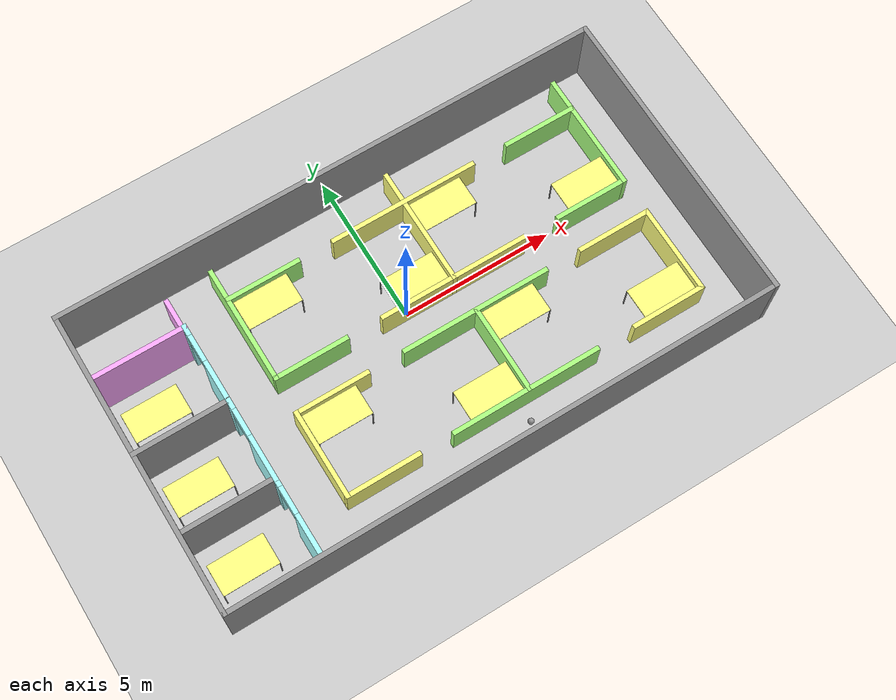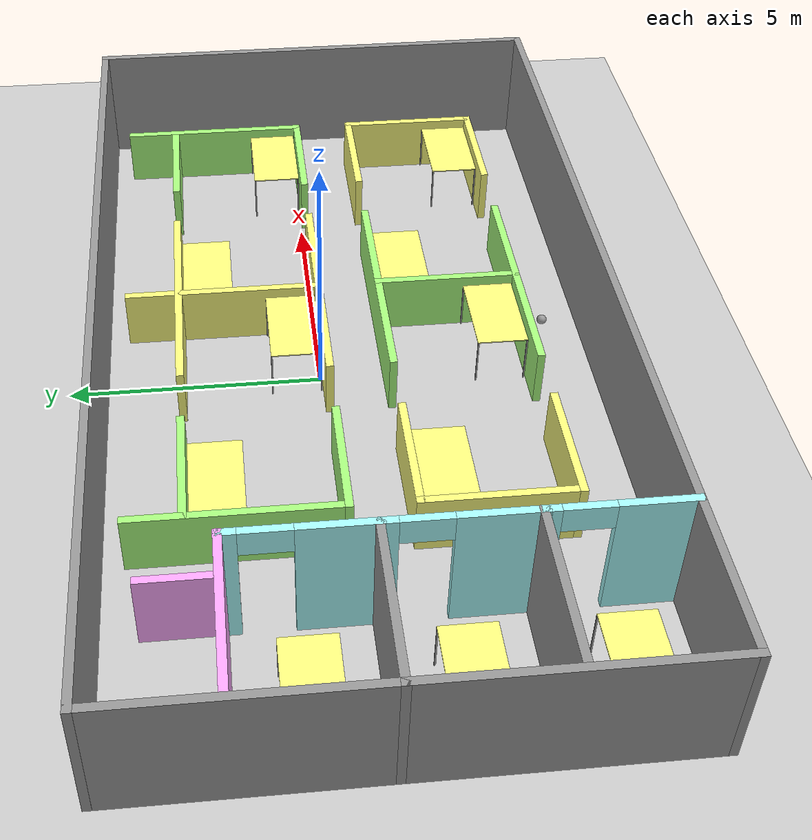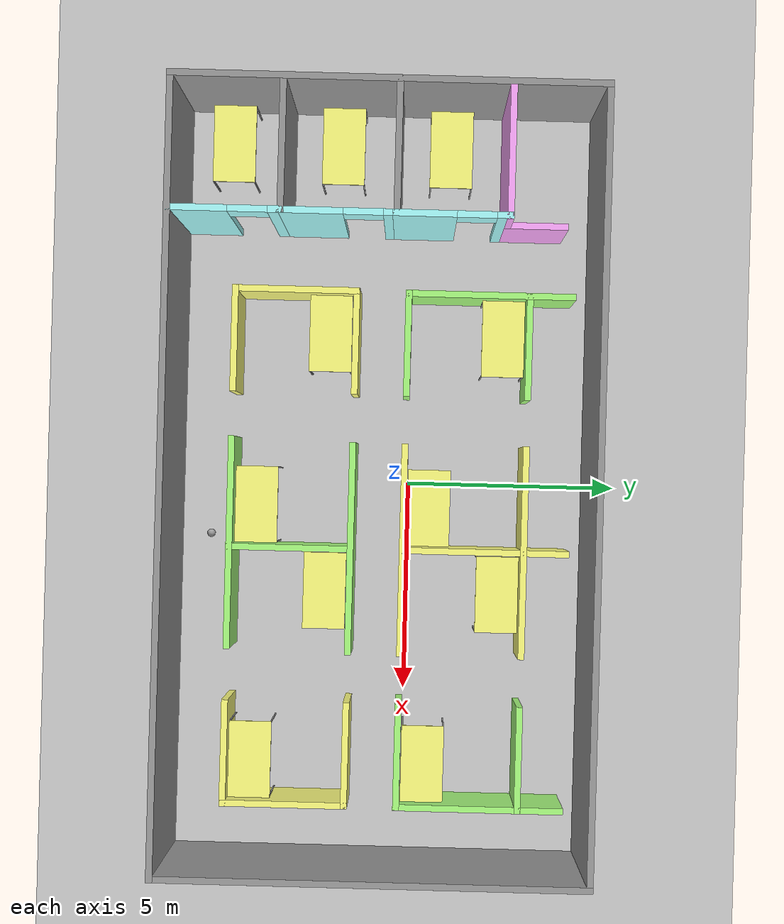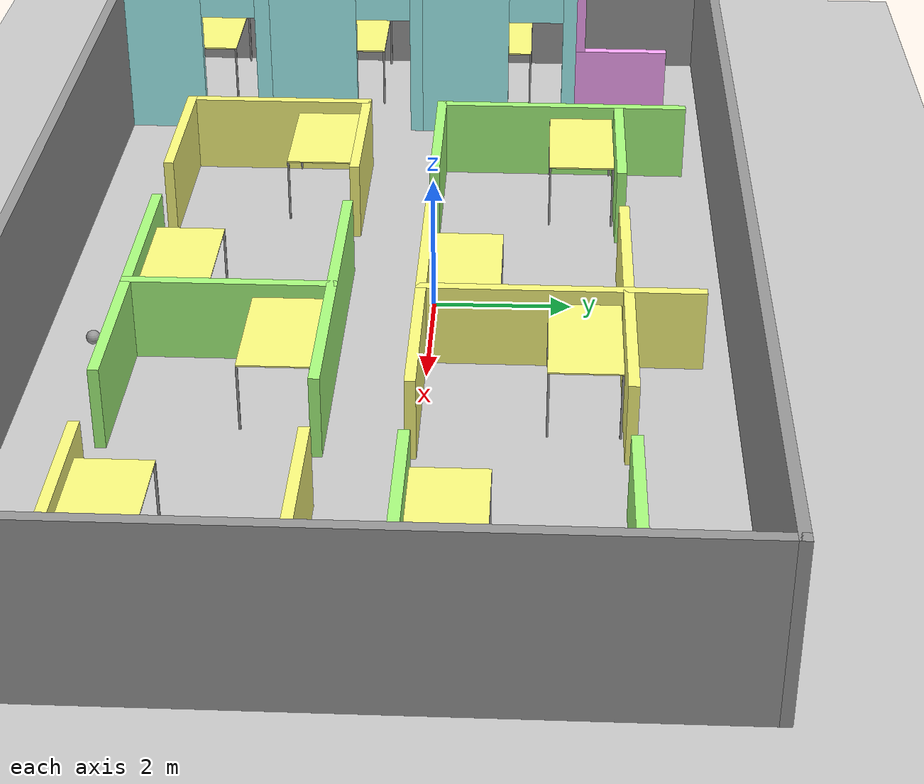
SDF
<sdf version="1.6">
 <world name="default">
  <light name="sun" type="directional">
   <pose>0 0 10 0 -0 0</pose>
   <diffuse>0.8 0.8 0.8 1</diffuse>
   <specular>0.1 0.1 0.1 1</specular>
   <attenuation>
    <range>1000</range>
    <constant>0.9</constant>
    <linear>0.01</linear>
    <quadratic>0.001</quadratic>
   </attenuation>
   <direction>-0.5 0.5 -1</direction>
  </light>
  <model name="ground_plane">
   <static>1</static>
   <link name="link">
    <collision name="collision">
     <geometry><plane><normal>0 0 1</normal><size>100 100</size></plane></geometry>
     <surface><friction><ode><mu>100</mu><mu2>50</mu2></ode></friction></surface>
    </collision>
    <visual name="visual">
     <cast_shadows>0</cast_shadows>
     <geometry><plane><normal>0 0 1</normal><size>100 100</size></plane></geometry>
     <material>
      <script><uri>file://media/materials/scripts/gazebo.material</uri><name>Gazebo/Grey</name></script>
     </material>
    </visual>
   </link>
  </model>
  <gravity>0 0 -9.8</gravity>
  <magnetic_field>6e-06 2.3e-05 -4.2e-05</magnetic_field>
  <atmosphere type="adiabatic"/>
  <physics name="default_physics" default="0" type="ode">
   <max_step_size>0.001</max_step_size>
   <real_time_factor>1</real_time_factor>
   <real_time_update_rate>1000</real_time_update_rate>
  </physics>
  <scene><ambient>0.4 0.4 0.4 1</ambient><background>0.7 0.7 0.7 1</background><shadows>1</shadows></scene>
  <spherical_coordinates>
   <surface_model>EARTH_WGS84</surface_model>
   <latitude_deg>0</latitude_deg>
   <longitude_deg>0</longitude_deg>
   <elevation>0</elevation>
   <heading_deg>0</heading_deg>
  </spherical_coordinates>
  <model name="custom_table">
   <link name="link_0">
    <pose>-1e-06 0 0.4 0 -0 0</pose>
    <inertial>
     <mass>1</mass>
     <inertia>
      <ixx>0.166667</ixx>
      <ixy>0</ixy>
      <ixz>0</ixz>
      <iyy>0.166667</iyy>
      <iyz>0</iyz>
      <izz>0.166667</izz>
     </inertia>
    </inertial>
    <visual name="visual">
     <geometry><box><size>1.8 1 0.02</size></box></geometry>
     <material>
      <lighting>1</lighting>
      <script><uri>file://media/materials/scripts/gazebo.material</uri><name>Gazebo/Grey</name></script>
      <shader type="pixel"><normal_map>__default__</normal_map></shader>
      <ambient>0.4 0.4 0.4 0.5</ambient>
      <diffuse>1 1 0.5 1</diffuse>
      <specular>0.4 0.4 0.4 1</specular>
      <emissive>0 0 0 1</emissive>
     </material>
    </visual>
    <collision name="collision">
     <geometry><box><size>1.8 1 0.02</size></box></geometry>
     <surface>
      <friction>
       <ode><mu>1</mu><mu2>1</mu2><fdir1>0 0 0</fdir1><slip1>0</slip1><slip2>0</slip2></ode>
       <torsional>
        <coefficient>1</coefficient>
        <patch_radius>0</patch_radius>
        <surface_radius>0</surface_radius>
        <use_patch_radius>1</use_patch_radius>
        <ode><slip>0</slip></ode>
       </torsional>
      </friction>
      <bounce><restitution_coefficient>0</restitution_coefficient><threshold>1e+06</threshold></bounce>
      <contact>
       <collide_without_contact>0</collide_without_contact>
       <collide_without_contact_bitmask>1</collide_without_contact_bitmask>
       <collide_bitmask>1</collide_bitmask>
       <ode>
        <soft_cfm>0</soft_cfm>
        <soft_erp>0.2</soft_erp>
        <kp>1e+13</kp>
        <kd>1</kd>
        <max_vel>0.01</max_vel>
        <min_depth>0</min_depth>
       </ode>
       <bullet>
        <split_impulse>1</split_impulse>
        <split_impulse_penetration_threshold>-0.01</split_impulse_penetration_threshold>
        <soft_cfm>0</soft_cfm>
        <soft_erp>0.2</soft_erp>
        <kp>1e+13</kp>
        <kd>1</kd>
       </bullet>
      </contact>
     </surface>
    </collision>
   </link>
   <link name="link_1_clone">
    <pose>0.884999 -0.485 -0.1 0 -0 0</pose>
    <inertial>
     <mass>1</mass>
     <inertia>
      <ixx>0.166667</ixx>
      <ixy>0</ixy>
      <ixz>0</ixz>
      <iyy>0.166667</iyy>
      <iyz>0</iyz>
      <izz>0.166667</izz>
     </inertia>
    </inertial>
    <visual name="visual">
     <geometry><box><size>0.03 0.03 0.98</size></box></geometry>
     <material>
      <lighting>1</lighting>
      <script><uri>file://media/materials/scripts/gazebo.material</uri><name>Gazebo/Grey</name></script>
      <shader type="pixel"><normal_map>__default__</normal_map></shader>
      <ambient>0.3 0.3 0.3 1</ambient>
      <diffuse>0.7 0.7 0.7 1</diffuse>
      <specular>0.01 0.01 0.01 1</specular>
      <emissive>0 0 0 1</emissive>
     </material>
    </visual>
    <collision name="collision">
     <geometry><box><size>0.03 0.03 0.98</size></box></geometry>
     <surface>
      <friction>
       <ode><mu>1</mu><mu2>1</mu2><fdir1>0 0 0</fdir1><slip1>0</slip1><slip2>0</slip2></ode>
       <torsional>
        <coefficient>1</coefficient>
        <patch_radius>0</patch_radius>
        <surface_radius>0</surface_radius>
        <use_patch_radius>1</use_patch_radius>
        <ode><slip>0</slip></ode>
       </torsional>
      </friction>
      <bounce><restitution_coefficient>0</restitution_coefficient><threshold>1e+06</threshold></bounce>
      <contact>
       <collide_without_contact>0</collide_without_contact>
       <collide_without_contact_bitmask>1</collide_without_contact_bitmask>
       <collide_bitmask>1</collide_bitmask>
       <ode>
        <soft_cfm>0</soft_cfm>
        <soft_erp>0.2</soft_erp>
        <kp>1e+13</kp>
        <kd>1</kd>
        <max_vel>0.01</max_vel>
        <min_depth>0</min_depth>
       </ode>
       <bullet>
        <split_impulse>1</split_impulse>
        <split_impulse_penetration_threshold>-0.01</split_impulse_penetration_threshold>
        <soft_cfm>0</soft_cfm>
        <soft_erp>0.2</soft_erp>
        <kp>1e+13</kp>
        <kd>1</kd>
       </bullet>
      </contact>
     </surface>
    </collision>
   </link>
   <link name="link_1_clone_0">
    <pose>-0.885001 0.485 -0.1 0 -0 0</pose>
    <inertial>
     <mass>1</mass>
     <inertia>
      <ixx>0.166667</ixx>
      <ixy>0</ixy>
      <ixz>0</ixz>
      <iyy>0.166667</iyy>
      <iyz>0</iyz>
      <izz>0.166667</izz>
     </inertia>
    </inertial>
    <visual name="visual">
     <geometry><box><size>0.03 0.03 0.98</size></box></geometry>
     <material>
      <lighting>1</lighting>
      <script><uri>file://media/materials/scripts/gazebo.material</uri><name>Gazebo/Grey</name></script>
      <shader type="pixel"><normal_map>__default__</normal_map></shader>
      <ambient>0.3 0.3 0.3 1</ambient>
      <diffuse>0.7 0.7 0.7 1</diffuse>
      <specular>0.01 0.01 0.01 1</specular>
      <emissive>0 0 0 1</emissive>
     </material>
    </visual>
    <collision name="collision">
     <geometry><box><size>0.03 0.03 0.98</size></box></geometry>
     <surface>
      <friction>
       <ode><mu>1</mu><mu2>1</mu2><fdir1>0 0 0</fdir1><slip1>0</slip1><slip2>0</slip2></ode>
       <torsional>
        <coefficient>1</coefficient>
        <patch_radius>0</patch_radius>
        <surface_radius>0</surface_radius>
        <use_patch_radius>1</use_patch_radius>
        <ode><slip>0</slip></ode>
       </torsional>
      </friction>
      <bounce><restitution_coefficient>0</restitution_coefficient><threshold>1e+06</threshold></bounce>
      <contact>
       <collide_without_contact>0</collide_without_contact>
       <collide_without_contact_bitmask>1</collide_without_contact_bitmask>
       <collide_bitmask>1</collide_bitmask>
       <ode>
        <soft_cfm>0</soft_cfm>
        <soft_erp>0.2</soft_erp>
        <kp>1e+13</kp>
        <kd>1</kd>
        <max_vel>0.01</max_vel>
        <min_depth>0</min_depth>
       </ode>
       <bullet>
        <split_impulse>1</split_impulse>
        <split_impulse_penetration_threshold>-0.01</split_impulse_penetration_threshold>
        <soft_cfm>0</soft_cfm>
        <soft_erp>0.2</soft_erp>
        <kp>1e+13</kp>
        <kd>1</kd>
       </bullet>
      </contact>
     </surface>
    </collision>
   </link>
   <link name="link_1_clone_clone">
    <pose>0.884999 0.485 -0.1 0 -0 0</pose>
    <inertial>
     <mass>1</mass>
     <inertia>
      <ixx>0.166667</ixx>
      <ixy>0</ixy>
      <ixz>0</ixz>
      <iyy>0.166667</iyy>
      <iyz>0</iyz>
      <izz>0.166667</izz>
     </inertia>
    </inertial>
    <visual name="visual">
     <geometry><box><size>0.03 0.03 0.98</size></box></geometry>
     <material>
      <lighting>1</lighting>
      <script><uri>file://media/materials/scripts/gazebo.material</uri><name>Gazebo/Grey</name></script>
      <shader type="pixel"><normal_map>__default__</normal_map></shader>
      <ambient>0.3 0.3 0.3 1</ambient>
      <diffuse>0.7 0.7 0.7 1</diffuse>
      <specular>0.01 0.01 0.01 1</specular>
      <emissive>0 0 0 1</emissive>
     </material>
    </visual>
    <collision name="collision">
     <geometry><box><size>0.03 0.03 0.98</size></box></geometry>
     <surface>
      <friction>
       <ode><mu>1</mu><mu2>1</mu2><fdir1>0 0 0</fdir1><slip1>0</slip1><slip2>0</slip2></ode>
       <torsional>
        <coefficient>1</coefficient>
        <patch_radius>0</patch_radius>
        <surface_radius>0</surface_radius>
        <use_patch_radius>1</use_patch_radius>
        <ode><slip>0</slip></ode>
       </torsional>
      </friction>
      <bounce><restitution_coefficient>0</restitution_coefficient><threshold>1e+06</threshold></bounce>
      <contact>
       <collide_without_contact>0</collide_without_contact>
       <collide_without_contact_bitmask>1</collide_without_contact_bitmask>
       <collide_bitmask>1</collide_bitmask>
       <ode>
        <soft_cfm>0</soft_cfm>
        <soft_erp>0.2</soft_erp>
        <kp>1e+13</kp>
        <kd>1</kd>
        <max_vel>0.01</max_vel>
        <min_depth>0</min_depth>
       </ode>
       <bullet>
        <split_impulse>1</split_impulse>
        <split_impulse_penetration_threshold>-0.01</split_impulse_penetration_threshold>
        <soft_cfm>0</soft_cfm>
        <soft_erp>0.2</soft_erp>
        <kp>1e+13</kp>
        <kd>1</kd>
       </bullet>
      </contact>
     </surface>
    </collision>
   </link>
   <link name="link_1_clone_clone_0">
    <pose>-0.885001 -0.485 -0.1 0 -0 0</pose>
    <inertial>
     <mass>1</mass>
     <inertia>
      <ixx>0.166667</ixx>
      <ixy>0</ixy>
      <ixz>0</ixz>
      <iyy>0.166667</iyy>
      <iyz>0</iyz>
      <izz>0.166667</izz>
     </inertia>
    </inertial>
    <visual name="visual">
     <geometry><box><size>0.03 0.03 0.98</size></box></geometry>
     <material>
      <lighting>1</lighting>
      <script><uri>file://media/materials/scripts/gazebo.material</uri><name>Gazebo/Grey</name></script>
      <shader type="pixel"><normal_map>__default__</normal_map></shader>
      <ambient>0.3 0.3 0.3 1</ambient>
      <diffuse>0.7 0.7 0.7 1</diffuse>
      <specular>0.01 0.01 0.01 1</specular>
      <emissive>0 0 0 1</emissive>
     </material>
    </visual>
    <collision name="collision">
     <geometry><box><size>0.03 0.03 0.98</size></box></geometry>
     <surface>
      <friction>
       <ode><mu>1</mu><mu2>1</mu2><fdir1>0 0 0</fdir1><slip1>0</slip1><slip2>0</slip2></ode>
       <torsional>
        <coefficient>1</coefficient>
        <patch_radius>0</patch_radius>
        <surface_radius>0</surface_radius>
        <use_patch_radius>1</use_patch_radius>
        <ode><slip>0</slip></ode>
       </torsional>
      </friction>
      <bounce><restitution_coefficient>0</restitution_coefficient><threshold>1e+06</threshold></bounce>
      <contact>
       <collide_without_contact>0</collide_without_contact>
       <collide_without_contact_bitmask>1</collide_without_contact_bitmask>
       <collide_bitmask>1</collide_bitmask>
       <ode>
        <soft_cfm>0</soft_cfm>
        <soft_erp>0.2</soft_erp>
        <kp>1e+13</kp>
        <kd>1</kd>
        <max_vel>0.01</max_vel>
        <min_depth>0</min_depth>
       </ode>
       <bullet>
        <split_impulse>1</split_impulse>
        <split_impulse_penetration_threshold>-0.01</split_impulse_penetration_threshold>
        <soft_cfm>0</soft_cfm>
        <soft_erp>0.2</soft_erp>
        <kp>1e+13</kp>
        <kd>1</kd>
       </bullet>
      </contact>
     </surface>
    </collision>
   </link>
   <joint name="link_0_JOINT_0" type="fixed">
    <parent>link_0</parent>
    <child>link_1_clone</child>
    <physics>
     <ode><limit><cfm>0</cfm><erp>0.2</erp></limit><suspension><cfm>0</cfm><erp>0.2</erp></suspension></ode>
    </physics>
   </joint>
   <joint name="link_0_JOINT_1" type="fixed">
    <parent>link_0</parent>
    <child>link_1_clone_0</child>
    <physics>
     <ode><limit><cfm>0</cfm><erp>0.2</erp></limit><suspension><cfm>0</cfm><erp>0.2</erp></suspension></ode>
    </physics>
   </joint>
   <joint name="link_0_JOINT_2" type="fixed">
    <parent>link_0</parent>
    <child>link_1_clone_clone</child>
    <physics>
     <ode><limit><cfm>0</cfm><erp>0.2</erp></limit><suspension><cfm>0</cfm><erp>0.2</erp></suspension></ode>
    </physics>
   </joint>
   <joint name="link_0_JOINT_3" type="fixed">
    <parent>link_0</parent>
    <child>link_1_clone_clone_0</child>
    <physics>
     <ode><limit><cfm>0</cfm><erp>0.2</erp></limit><suspension><cfm>0</cfm><erp>0.2</erp></suspension></ode>
    </physics>
   </joint>
   <static>1</static>
   <pose>-7.89321 0.822776 0.6 0 -0 0</pose>
  </model>
  <model name="sr_office">
   <pose>-0.02579 -0.62634 0 0 -0 0</pose>
   <link name="Wall_11">
    <pose>-6.0106 -3.67095 0 0 -0 1.57171</pose>
    <visual name="Wall_11_Visual_0">
     <pose>-0.611587 0 1.25 0 -0 0</pose>
     <geometry><box><size>1.41152 0.15 2.5</size></box></geometry>
     <material>
      <script><uri>file://media/materials/scripts/gazebo.material</uri><name>Gazebo/Grey</name></script>
      <ambient>0.666667 1 1 1</ambient>
     </material>
     <meta><layer>0</layer></meta>
    </visual>
    <collision name="Wall_11_Collision_0">
     <geometry><box><size>1.41152 0.15 2.5</size></box></geometry>
     <pose>-0.611587 0 1.25 0 -0 0</pose>
    </collision>
    <visual name="Wall_11_Visual_1">
     <pose>1.15576 0 1.25 0 -0 0</pose>
     <geometry><box><size>0.323174 0.15 2.5</size></box></geometry>
     <material>
      <script><uri>file://media/materials/scripts/gazebo.material</uri><name>Gazebo/Grey</name></script>
      <ambient>0.666667 1 1 1</ambient>
     </material>
     <meta><layer>0</layer></meta>
    </visual>
    <collision name="Wall_11_Collision_1">
     <geometry><box><size>0.323174 0.15 2.5</size></box></geometry>
     <pose>1.15576 0 1.25 0 -0 0</pose>
    </collision>
    <visual name="Wall_11_Visual_2">
     <pose>0.544173 0 2.25 0 -0 0</pose>
     <geometry><box><size>0.9 0.15 0.5</size></box></geometry>
     <material>
      <script><uri>file://media/materials/scripts/gazebo.material</uri><name>Gazebo/Grey</name></script>
      <ambient>0.666667 1 1 1</ambient>
     </material>
     <meta><layer>0</layer></meta>
    </visual>
    <collision name="Wall_11_Collision_2">
     <geometry><box><size>0.9 0.15 0.5</size></box></geometry>
     <pose>0.544173 0 2.25 0 -0 0</pose>
    </collision>
   </link>
   <link name="Wall_12">
    <collision name="Wall_12_Collision">
     <geometry><box><size>3 0.15 2.5</size></box></geometry>
     <pose>0 0 1.25 0 -0 0</pose>
    </collision>
    <visual name="Wall_12_Visual">
     <pose>0 0 1.25 0 -0 0</pose>
     <geometry><box><size>3 0.15 2.5</size></box></geometry>
     <material>
      <script><uri>file://media/materials/scripts/gazebo.material</uri><name>Gazebo/Grey</name></script>
      <ambient>1 1 1 1</ambient>
     </material>
     <meta><layer>0</layer></meta>
    </visual>
    <pose>-7.43674 -2.38916 0 0 -0 3.14159</pose>
   </link>
   <link name="Wall_19">
    <pose>-6.01174 1.48653 0 0 -0 1.5708</pose>
    <visual name="Wall_19_Visual_0">
     <pose>-0.636752 0 1.25 0 -0 0</pose>
     <geometry><box><size>1.44348 0.15 2.5</size></box></geometry>
     <material>
      <script><uri>file://media/materials/scripts/gazebo.material</uri><name>Gazebo/Grey</name></script>
      <ambient>0.666667 1 1 1</ambient>
     </material>
     <meta><layer>0</layer></meta>
    </visual>
    <collision name="Wall_19_Collision_0">
     <geometry><box><size>1.44348 0.15 2.5</size></box></geometry>
     <pose>-0.636752 0 1.25 0 -0 0</pose>
    </collision>
    <visual name="Wall_19_Visual_1">
     <pose>1.17174 0 1.25 0 -0 0</pose>
     <geometry><box><size>0.373505 0.15 2.5</size></box></geometry>
     <material>
      <script><uri>file://media/materials/scripts/gazebo.material</uri><name>Gazebo/Grey</name></script>
      <ambient>0.666667 1 1 1</ambient>
     </material>
     <meta><layer>0</layer></meta>
    </visual>
    <collision name="Wall_19_Collision_1">
     <geometry><box><size>0.373505 0.15 2.5</size></box></geometry>
     <pose>1.17174 0 1.25 0 -0 0</pose>
    </collision>
    <visual name="Wall_19_Visual_2">
     <pose>0.534986 0 2.25 0 -0 0</pose>
     <geometry><box><size>0.9 0.15 0.5</size></box></geometry>
     <material>
      <script><uri>file://media/materials/scripts/gazebo.material</uri><name>Gazebo/Grey</name></script>
      <ambient>0.666667 1 1 1</ambient>
     </material>
     <meta><layer>0</layer></meta>
    </visual>
    <collision name="Wall_19_Collision_2">
     <geometry><box><size>0.9 0.15 0.5</size></box></geometry>
     <pose>0.534986 0 2.25 0 -0 0</pose>
    </collision>
   </link>
   <link name="Wall_2">
    <collision name="Wall_2_Collision">
     <geometry><box><size>10 0.15 2.5</size></box></geometry>
     <pose>0 0 1.25 0 -0 0</pose>
    </collision>
    <visual name="Wall_2_Visual">
     <pose>0 0 1.25 0 -0 0</pose>
     <geometry><box><size>10 0.15 2.5</size></box></geometry>
     <material>
      <script><uri>file://media/materials/scripts/gazebo.material</uri><name>Gazebo/Grey</name></script>
      <ambient>1 1 1 1</ambient>
     </material>
     <meta><layer>0</layer></meta>
    </visual>
    <pose>-9.01174 2.1e-05 0 0 0 -1.5708</pose>
   </link>
   <link name="Wall_20">
    <collision name="Wall_20_Collision">
     <geometry><box><size>3 0.15 2.5</size></box></geometry>
     <pose>0 0 1.25 0 -0 0</pose>
    </collision>
    <visual name="Wall_20_Visual">
     <pose>0 0 1.25 0 -0 0</pose>
     <geometry><box><size>3 0.15 2.5</size></box></geometry>
     <material>
      <script><uri>file://media/materials/scripts/gazebo.material</uri><name>Gazebo/Grey</name></script>
      <ambient>1 0.666667 1 1</ambient>
     </material>
     <meta><layer>0</layer></meta>
    </visual>
    <pose>-7.43674 2.77002 0 0 -0 3.14159</pose>
   </link>
   <link name="Wall_22">
    <collision name="Wall_22_Collision">
     <geometry><box><size>1.5 0.15 1.5</size></box></geometry>
     <pose>0 0 0.75 0 -0 0</pose>
    </collision>
    <visual name="Wall_22_Visual">
     <pose>0 0 0.75 0 -0 0</pose>
     <geometry><box><size>1.5 0.15 1.5</size></box></geometry>
     <material>
      <script><uri>file://media/materials/scripts/gazebo.material</uri><name>Gazebo/Grey</name></script>
      <ambient>1 0.666667 1 1</ambient>
     </material>
     <meta><layer>0</layer></meta>
    </visual>
    <pose>-6.01174 3.44502 0 0 -0 1.5708</pose>
   </link>
   <link name="Wall_24">
    <collision name="Wall_24_Collision">
     <geometry><box><size>2.5 0.15 1.2</size></box></geometry>
     <pose>0 0 0.6 0 -0 0</pose>
    </collision>
    <visual name="Wall_24_Visual">
     <pose>0 0 0.6 0 -0 0</pose>
     <geometry><box><size>2.5 0.15 1.2</size></box></geometry>
     <material>
      <script><uri>file://media/materials/scripts/gazebo.material</uri><name>Gazebo/Grey</name></script>
      <ambient>1 1 0.498039 1</ambient>
     </material>
     <meta><layer>0</layer></meta>
    </visual>
    <pose>-3.28174 -3.54698 0 0 -0 3.14159</pose>
   </link>
   <link name="Wall_25">
    <collision name="Wall_25_Collision">
     <geometry><box><size>3.0027 0.15 1.2</size></box></geometry>
     <pose>0 0 0.6 0 -0 0</pose>
    </collision>
    <visual name="Wall_25_Visual">
     <pose>0 0 0.6 0 -0 0</pose>
     <geometry><box><size>3.0027 0.15 1.2</size></box></geometry>
     <material>
      <script><uri>file://media/materials/scripts/gazebo.material</uri><name>Gazebo/Grey</name></script>
      <ambient>1 1 0.498039 1</ambient>
     </material>
     <meta><layer>0</layer></meta>
    </visual>
    <pose>-4.45674 -2.12048 0 0 -0 1.5708</pose>
   </link>
   <link name="Wall_26">
    <collision name="Wall_26_Collision">
     <geometry><box><size>2.5 0.15 1.2</size></box></geometry>
     <pose>0 0 0.6 0 -0 0</pose>
    </collision>
    <visual name="Wall_26_Visual">
     <pose>0 0 0.6 0 -0 0</pose>
     <geometry><box><size>2.5 0.15 1.2</size></box></geometry>
     <material>
      <script><uri>file://media/materials/scripts/gazebo.material</uri><name>Gazebo/Grey</name></script>
      <ambient>1 1 0.498039 1</ambient>
     </material>
     <meta><layer>0</layer></meta>
    </visual>
    <pose>-3.28174 -0.693979 0 0 -0 0</pose>
   </link>
   <link name="Wall_29">
    <collision name="Wall_29_Collision">
     <geometry><box><size>5 0.15 1.2</size></box></geometry>
     <pose>0 0 0.6 0 -0 0</pose>
    </collision>
    <visual name="Wall_29_Visual">
     <pose>0 0 0.6 0 -0 0</pose>
     <geometry><box><size>5 0.15 1.2</size></box></geometry>
     <material>
      <script><uri>file://media/materials/scripts/gazebo.material</uri><name>Gazebo/Grey</name></script>
      <ambient>0.666667 1 0.498039 1</ambient>
     </material>
     <meta><layer>0</layer></meta>
    </visual>
    <pose>1.59726 -0.693979 0 0 -0 0</pose>
   </link>
   <link name="Wall_3">
    <collision name="Wall_3_Collision">
     <geometry><box><size>18.1739 0.15 2.5</size></box></geometry>
     <pose>0 0 1.25 0 -0 0</pose>
    </collision>
    <visual name="Wall_3_Visual">
     <pose>0 0 1.25 0 -0 0</pose>
     <geometry><box><size>18.1739 0.15 2.5</size></box></geometry>
     <material>
      <script><uri>file://media/materials/scripts/gazebo.material</uri><name>Gazebo/Grey</name></script>
      <ambient>1 1 1 1</ambient>
     </material>
     <meta><layer>0</layer></meta>
    </visual>
    <pose>0 -4.925 0 0 0 -2e-06</pose>
   </link>
   <link name="Wall_33">
    <collision name="Wall_33_Collision">
     <geometry><box><size>5 0.15 1.2</size></box></geometry>
     <pose>0 0 0.6 0 -0 0</pose>
    </collision>
    <visual name="Wall_33_Visual">
     <pose>0 0 0.6 0 -0 0</pose>
     <geometry><box><size>5 0.15 1.2</size></box></geometry>
     <material>
      <script><uri>file://media/materials/scripts/gazebo.material</uri><name>Gazebo/Grey</name></script>
      <ambient>0.666667 1 0.498039 1</ambient>
     </material>
     <meta><layer>0</layer></meta>
    </visual>
    <pose>1.51726 -3.54398 0 0 -0 0</pose>
   </link>
   <link name="Wall_36">
    <collision name="Wall_36_Collision">
     <geometry><box><size>2.999 0.15 1.2</size></box></geometry>
     <pose>0 0 0.6 0 -0 0</pose>
    </collision>
    <visual name="Wall_36_Visual">
     <pose>0 0 0.6 0 -0 0</pose>
     <geometry><box><size>2.999 0.15 1.2</size></box></geometry>
     <material>
      <script><uri>file://media/materials/scripts/gazebo.material</uri><name>Gazebo/Grey</name></script>
      <ambient>0.666667 1 0.498039 1</ambient>
     </material>
     <meta><layer>0</layer></meta>
    </visual>
    <pose>1.61226 -2.11848 0 0 -0 1.5708</pose>
   </link>
   <link name="Wall_38">
    <collision name="Wall_38_Collision">
     <geometry><box><size>2.5 0.15 1.2</size></box></geometry>
     <pose>0 0 0.6 0 -0 0</pose>
    </collision>
    <visual name="Wall_38_Visual">
     <pose>0 0 0.6 0 -0 0</pose>
     <geometry><box><size>2.5 0.15 1.2</size></box></geometry>
     <material>
      <script><uri>file://media/materials/scripts/gazebo.material</uri><name>Gazebo/Grey</name></script>
      <ambient>1 1 0.498039 1</ambient>
     </material>
     <meta><layer>0</layer></meta>
    </visual>
    <pose>6.46326 -0.693979 0 0 -0 0</pose>
   </link>
   <link name="Wall_39">
    <collision name="Wall_39_Collision">
     <geometry><box><size>3 0.15 1.2</size></box></geometry>
     <pose>0 0 0.6 0 -0 0</pose>
    </collision>
    <visual name="Wall_39_Visual">
     <pose>0 0 0.6 0 -0 0</pose>
     <geometry><box><size>3 0.15 1.2</size></box></geometry>
     <material>
      <script><uri>file://media/materials/scripts/gazebo.material</uri><name>Gazebo/Grey</name></script>
      <ambient>1 1 0.498039 1</ambient>
     </material>
     <meta><layer>0</layer></meta>
    </visual>
    <pose>7.63826 -2.11898 0 0 0 -1.5708</pose>
   </link>
   <link name="Wall_4">
    <collision name="Wall_4_Collision">
     <geometry><box><size>10 0.15 2.5</size></box></geometry>
     <pose>0 0 1.25 0 -0 0</pose>
    </collision>
    <visual name="Wall_4_Visual">
     <pose>0 0 1.25 0 -0 0</pose>
     <geometry><box><size>10 0.15 2.5</size></box></geometry>
     <material>
      <script><uri>file://media/materials/scripts/gazebo.material</uri><name>Gazebo/Grey</name></script>
      <ambient>1 1 1 1</ambient>
     </material>
     <meta><layer>0</layer></meta>
    </visual>
    <pose>9.01174 -2.1e-05 0 0 -0 1.5708</pose>
   </link>
   <link name="Wall_40">
    <collision name="Wall_40_Collision">
     <geometry><box><size>2.5 0.15 1.2</size></box></geometry>
     <pose>0 0 0.6 0 -0 0</pose>
    </collision>
    <visual name="Wall_40_Visual">
     <pose>0 0 0.6 0 -0 0</pose>
     <geometry><box><size>2.5 0.15 1.2</size></box></geometry>
     <material>
      <script><uri>file://media/materials/scripts/gazebo.material</uri><name>Gazebo/Grey</name></script>
      <ambient>1 1 0.498039 1</ambient>
     </material>
     <meta><layer>0</layer></meta>
    </visual>
    <pose>6.46326 -3.54398 0 0 -0 3.14159</pose>
   </link>
   <link name="Wall_42">
    <collision name="Wall_42_Collision">
     <geometry><box><size>2.5 0.15 1.2</size></box></geometry>
     <pose>0 0 0.6 0 -0 0</pose>
    </collision>
    <visual name="Wall_42_Visual">
     <pose>0 0 0.6 0 -0 0</pose>
     <geometry><box><size>2.5 0.15 1.2</size></box></geometry>
     <material>
      <script><uri>file://media/materials/scripts/gazebo.material</uri><name>Gazebo/Grey</name></script>
      <ambient>0.666667 1 0.498039 1</ambient>
     </material>
     <meta><layer>0</layer></meta>
    </visual>
    <pose>-3.25874 0.531021 0 0 -0 3.14159</pose>
   </link>
   <link name="Wall_43">
    <collision name="Wall_43_Collision">
     <geometry><box><size>4.00484 0.15 1.2</size></box></geometry>
     <pose>0 0 0.6 0 -0 0</pose>
    </collision>
    <visual name="Wall_43_Visual">
     <pose>0 0 0.6 0 -0 0</pose>
     <geometry><box><size>4.00484 0.15 1.2</size></box></geometry>
     <material>
      <script><uri>file://media/materials/scripts/gazebo.material</uri><name>Gazebo/Grey</name></script>
      <ambient>0.666667 1 0.498039 1</ambient>
     </material>
     <meta><layer>0</layer></meta>
    </visual>
    <pose>-4.43374 2.45852 0 0 -0 1.5708</pose>
   </link>
   <link name="Wall_45">
    <collision name="Wall_45_Collision">
     <geometry><box><size>2.5 0.15 1.2</size></box></geometry>
     <pose>0 0 0.6 0 -0 0</pose>
    </collision>
    <visual name="Wall_45_Visual">
     <pose>0 0 0.6 0 -0 0</pose>
     <geometry><box><size>2.5 0.15 1.2</size></box></geometry>
     <material>
      <script><uri>file://media/materials/scripts/gazebo.material</uri><name>Gazebo/Grey</name></script>
      <ambient>0.666667 1 0.498039 1</ambient>
     </material>
     <meta><layer>0</layer></meta>
    </visual>
    <pose>-3.24374 3.38102 0 0 -0 0</pose>
   </link>
   <link name="Wall_47">
    <collision name="Wall_47_Collision">
     <geometry><box><size>5 0.15 1.2</size></box></geometry>
     <pose>0 0 0.6 0 -0 0</pose>
    </collision>
    <visual name="Wall_47_Visual">
     <pose>0 0 0.6 0 -0 0</pose>
     <geometry><box><size>5 0.15 1.2</size></box></geometry>
     <material>
      <script><uri>file://media/materials/scripts/gazebo.material</uri><name>Gazebo/Grey</name></script>
      <ambient>1 1 0.498039 1</ambient>
     </material>
     <meta><layer>0</layer></meta>
    </visual>
    <pose>1.59726 0.531021 0 0 -0 0</pose>
   </link>
   <link name="Wall_49">
    <collision name="Wall_49_Collision">
     <geometry><box><size>4 0.15 1.2</size></box></geometry>
     <pose>0 0 0.6 0 -0 0</pose>
    </collision>
    <visual name="Wall_49_Visual">
     <pose>0 0 0.6 0 -0 0</pose>
     <geometry><box><size>4 0.15 1.2</size></box></geometry>
     <material>
      <script><uri>file://media/materials/scripts/gazebo.material</uri><name>Gazebo/Grey</name></script>
      <ambient>1 1 0.498039 1</ambient>
     </material>
     <meta><layer>0</layer></meta>
    </visual>
    <pose>1.60426 2.45602 0 0 -0 1.5708</pose>
   </link>
   <link name="Wall_5">
    <collision name="Wall_5_Collision">
     <geometry><box><size>18.1739 0.15 2.5</size></box></geometry>
     <pose>0 0 1.25 0 -0 0</pose>
    </collision>
    <visual name="Wall_5_Visual">
     <pose>0 0 1.25 0 -0 0</pose>
     <geometry><box><size>18.1739 0.15 2.5</size></box></geometry>
     <material>
      <script><uri>file://media/materials/scripts/gazebo.material</uri><name>Gazebo/Grey</name></script>
      <ambient>1 1 1 1</ambient>
     </material>
     <meta><layer>0</layer></meta>
    </visual>
    <pose>0 4.925 0 0 -0 3.14159</pose>
   </link>
   <link name="Wall_51">
    <collision name="Wall_51_Collision">
     <geometry><box><size>5 0.15 1.2</size></box></geometry>
     <pose>0 0 0.6 0 -0 0</pose>
    </collision>
    <visual name="Wall_51_Visual">
     <pose>0 0 0.6 0 -0 0</pose>
     <geometry><box><size>5 0.15 1.2</size></box></geometry>
     <material>
      <script><uri>file://media/materials/scripts/gazebo.material</uri><name>Gazebo/Grey</name></script>
      <ambient>1 1 0.498039 1</ambient>
     </material>
     <meta><layer>0</layer></meta>
    </visual>
    <pose>1.59726 3.38102 0 0 -0 0</pose>
   </link>
   <link name="Wall_53">
    <collision name="Wall_53_Collision">
     <geometry><box><size>2.5 0.15 1.2</size></box></geometry>
     <pose>0 0 0.6 0 -0 0</pose>
    </collision>
    <visual name="Wall_53_Visual">
     <pose>0 0 0.6 0 -0 0</pose>
     <geometry><box><size>2.5 0.15 1.2</size></box></geometry>
     <material>
      <script><uri>file://media/materials/scripts/gazebo.material</uri><name>Gazebo/Grey</name></script>
      <ambient>0.666667 1 0.498039 1</ambient>
     </material>
     <meta><layer>0</layer></meta>
    </visual>
    <pose>6.46326 0.531021 0 0 -0 0</pose>
   </link>
   <link name="Wall_55">
    <collision name="Wall_55_Collision">
     <geometry><box><size>2.5 0.15 1.2</size></box></geometry>
     <pose>0 0 0.6 0 -0 0</pose>
    </collision>
    <visual name="Wall_55_Visual">
     <pose>0 0 0.6 0 -0 0</pose>
     <geometry><box><size>2.5 0.15 1.2</size></box></geometry>
     <material>
      <script><uri>file://media/materials/scripts/gazebo.material</uri><name>Gazebo/Grey</name></script>
      <ambient>0.666667 1 0.498039 1</ambient>
     </material>
     <meta><layer>0</layer></meta>
    </visual>
    <pose>6.46326 3.38102 0 0 -0 3.14159</pose>
   </link>
   <link name="Wall_57">
    <collision name="Wall_57_Collision">
     <geometry><box><size>4 0.15 1.2</size></box></geometry>
     <pose>0 0 0.6 0 -0 0</pose>
    </collision>
    <visual name="Wall_57_Visual">
     <pose>0 0 0.6 0 -0 0</pose>
     <geometry><box><size>4 0.15 1.2</size></box></geometry>
     <material>
      <script><uri>file://media/materials/scripts/gazebo.material</uri><name>Gazebo/Grey</name></script>
      <ambient>0.666667 1 0.498039 1</ambient>
     </material>
     <meta><layer>0</layer></meta>
    </visual>
    <pose>7.63826 2.45602 0 0 -0 1.5708</pose>
   </link>
   <link name="Wall_7">
    <pose>-6.01174 -1.11278 0 0 -0 1.5708</pose>
    <visual name="Wall_7_Visual_0">
     <pose>-0.629255 0 1.25 0 -0 0</pose>
     <geometry><box><size>1.52314 0.15 2.5</size></box></geometry>
     <material>
      <script><uri>file://media/materials/scripts/gazebo.material</uri><name>Gazebo/Grey</name></script>
      <ambient>0.666667 1 1 1</ambient>
     </material>
     <meta><layer>0</layer></meta>
    </visual>
    <collision name="Wall_7_Collision_0">
     <geometry><box><size>1.52314 0.15 2.5</size></box></geometry>
     <pose>-0.629255 0 1.25 0 -0 0</pose>
    </collision>
    <visual name="Wall_7_Visual_1">
     <pose>1.21157 0 1.25 0 -0 0</pose>
     <geometry><box><size>0.358509 0.15 2.5</size></box></geometry>
     <material>
      <script><uri>file://media/materials/scripts/gazebo.material</uri><name>Gazebo/Grey</name></script>
      <ambient>0.666667 1 1 1</ambient>
     </material>
     <meta><layer>0</layer></meta>
    </visual>
    <collision name="Wall_7_Collision_1">
     <geometry><box><size>0.358509 0.15 2.5</size></box></geometry>
     <pose>1.21157 0 1.25 0 -0 0</pose>
    </collision>
    <visual name="Wall_7_Visual_2">
     <pose>0.582314 0 2.25 0 -0 0</pose>
     <geometry><box><size>0.9 0.15 0.5</size></box></geometry>
     <material>
      <script><uri>file://media/materials/scripts/gazebo.material</uri><name>Gazebo/Grey</name></script>
      <ambient>0.666667 1 1 1</ambient>
     </material>
     <meta><layer>0</layer></meta>
    </visual>
    <collision name="Wall_7_Collision_2">
     <geometry><box><size>0.9 0.15 0.5</size></box></geometry>
     <pose>0.582314 0 2.25 0 -0 0</pose>
    </collision>
   </link>
   <link name="Wall_8">
    <collision name="Wall_8_Collision">
     <geometry><box><size>3.15 0.15 2.5</size></box></geometry>
     <pose>0 0 1.25 0 -0 0</pose>
    </collision>
    <visual name="Wall_8_Visual">
     <pose>0 0 1.25 0 -0 0</pose>
     <geometry><box><size>3.15 0.15 2.5</size></box></geometry>
     <material>
      <script><uri>file://media/materials/scripts/gazebo.material</uri><name>Gazebo/Grey</name></script>
      <ambient>1 1 1 1</ambient>
     </material>
     <meta><layer>0</layer></meta>
    </visual>
    <pose>-7.51174 0.222766 0 0 -0 3.14159</pose>
   </link>
   <static>1</static>
  </model>
  <model name="custom_table_clone">
   <link name="link_0">
    <pose>-1e-06 0 0.4 0 -0 0</pose>
    <inertial>
     <mass>1</mass>
     <inertia>
      <ixx>0.166667</ixx>
      <ixy>0</ixy>
      <ixz>0</ixz>
      <iyy>0.166667</iyy>
      <iyz>0</iyz>
      <izz>0.166667</izz>
     </inertia>
    </inertial>
    <visual name="visual">
     <geometry><box><size>1.8 1 0.02</size></box></geometry>
     <material>
      <lighting>1</lighting>
      <script><uri>file://media/materials/scripts/gazebo.material</uri><name>Gazebo/Grey</name></script>
      <shader type="pixel"><normal_map>__default__</normal_map></shader>
      <ambient>0.4 0.4 0.4 0.5</ambient>
      <diffuse>1 1 0.5 1</diffuse>
      <specular>0.4 0.4 0.4 1</specular>
      <emissive>0 0 0 1</emissive>
     </material>
    </visual>
    <collision name="collision">
     <geometry><box><size>1.8 1 0.02</size></box></geometry>
     <surface>
      <friction>
       <ode><mu>1</mu><mu2>1</mu2><fdir1>0 0 0</fdir1><slip1>0</slip1><slip2>0</slip2></ode>
       <torsional>
        <coefficient>1</coefficient>
        <patch_radius>0</patch_radius>
        <surface_radius>0</surface_radius>
        <use_patch_radius>1</use_patch_radius>
        <ode><slip>0</slip></ode>
       </torsional>
      </friction>
      <bounce><restitution_coefficient>0</restitution_coefficient><threshold>1e+06</threshold></bounce>
      <contact>
       <collide_without_contact>0</collide_without_contact>
       <collide_without_contact_bitmask>1</collide_without_contact_bitmask>
       <collide_bitmask>1</collide_bitmask>
       <ode>
        <soft_cfm>0</soft_cfm>
        <soft_erp>0.2</soft_erp>
        <kp>1e+13</kp>
        <kd>1</kd>
        <max_vel>0.01</max_vel>
        <min_depth>0</min_depth>
       </ode>
       <bullet>
        <split_impulse>1</split_impulse>
        <split_impulse_penetration_threshold>-0.01</split_impulse_penetration_threshold>
        <soft_cfm>0</soft_cfm>
        <soft_erp>0.2</soft_erp>
        <kp>1e+13</kp>
        <kd>1</kd>
       </bullet>
      </contact>
     </surface>
    </collision>
   </link>
   <link name="link_1_clone">
    <pose>0.884999 -0.485 -0.1 0 -0 0</pose>
    <inertial>
     <mass>1</mass>
     <inertia>
      <ixx>0.166667</ixx>
      <ixy>0</ixy>
      <ixz>0</ixz>
      <iyy>0.166667</iyy>
      <iyz>0</iyz>
      <izz>0.166667</izz>
     </inertia>
    </inertial>
    <visual name="visual">
     <geometry><box><size>0.03 0.03 0.98</size></box></geometry>
     <material>
      <lighting>1</lighting>
      <script><uri>file://media/materials/scripts/gazebo.material</uri><name>Gazebo/Grey</name></script>
      <shader type="pixel"><normal_map>__default__</normal_map></shader>
      <ambient>0.3 0.3 0.3 1</ambient>
      <diffuse>0.7 0.7 0.7 1</diffuse>
      <specular>0.01 0.01 0.01 1</specular>
      <emissive>0 0 0 1</emissive>
     </material>
    </visual>
    <collision name="collision">
     <geometry><box><size>0.03 0.03 0.98</size></box></geometry>
     <surface>
      <friction>
       <ode><mu>1</mu><mu2>1</mu2><fdir1>0 0 0</fdir1><slip1>0</slip1><slip2>0</slip2></ode>
       <torsional>
        <coefficient>1</coefficient>
        <patch_radius>0</patch_radius>
        <surface_radius>0</surface_radius>
        <use_patch_radius>1</use_patch_radius>
        <ode><slip>0</slip></ode>
       </torsional>
      </friction>
      <bounce><restitution_coefficient>0</restitution_coefficient><threshold>1e+06</threshold></bounce>
      <contact>
       <collide_without_contact>0</collide_without_contact>
       <collide_without_contact_bitmask>1</collide_without_contact_bitmask>
       <collide_bitmask>1</collide_bitmask>
       <ode>
        <soft_cfm>0</soft_cfm>
        <soft_erp>0.2</soft_erp>
        <kp>1e+13</kp>
        <kd>1</kd>
        <max_vel>0.01</max_vel>
        <min_depth>0</min_depth>
       </ode>
       <bullet>
        <split_impulse>1</split_impulse>
        <split_impulse_penetration_threshold>-0.01</split_impulse_penetration_threshold>
        <soft_cfm>0</soft_cfm>
        <soft_erp>0.2</soft_erp>
        <kp>1e+13</kp>
        <kd>1</kd>
       </bullet>
      </contact>
     </surface>
    </collision>
   </link>
   <link name="link_1_clone_0">
    <pose>-0.885001 0.485 -0.1 0 -0 0</pose>
    <inertial>
     <mass>1</mass>
     <inertia>
      <ixx>0.166667</ixx>
      <ixy>0</ixy>
      <ixz>0</ixz>
      <iyy>0.166667</iyy>
      <iyz>0</iyz>
      <izz>0.166667</izz>
     </inertia>
    </inertial>
    <visual name="visual">
     <geometry><box><size>0.03 0.03 0.98</size></box></geometry>
     <material>
      <lighting>1</lighting>
      <script><uri>file://media/materials/scripts/gazebo.material</uri><name>Gazebo/Grey</name></script>
      <shader type="pixel"><normal_map>__default__</normal_map></shader>
      <ambient>0.3 0.3 0.3 1</ambient>
      <diffuse>0.7 0.7 0.7 1</diffuse>
      <specular>0.01 0.01 0.01 1</specular>
      <emissive>0 0 0 1</emissive>
     </material>
    </visual>
    <collision name="collision">
     <geometry><box><size>0.03 0.03 0.98</size></box></geometry>
     <surface>
      <friction>
       <ode><mu>1</mu><mu2>1</mu2><fdir1>0 0 0</fdir1><slip1>0</slip1><slip2>0</slip2></ode>
       <torsional>
        <coefficient>1</coefficient>
        <patch_radius>0</patch_radius>
        <surface_radius>0</surface_radius>
        <use_patch_radius>1</use_patch_radius>
        <ode><slip>0</slip></ode>
       </torsional>
      </friction>
      <bounce><restitution_coefficient>0</restitution_coefficient><threshold>1e+06</threshold></bounce>
      <contact>
       <collide_without_contact>0</collide_without_contact>
       <collide_without_contact_bitmask>1</collide_without_contact_bitmask>
       <collide_bitmask>1</collide_bitmask>
       <ode>
        <soft_cfm>0</soft_cfm>
        <soft_erp>0.2</soft_erp>
        <kp>1e+13</kp>
        <kd>1</kd>
        <max_vel>0.01</max_vel>
        <min_depth>0</min_depth>
       </ode>
       <bullet>
        <split_impulse>1</split_impulse>
        <split_impulse_penetration_threshold>-0.01</split_impulse_penetration_threshold>
        <soft_cfm>0</soft_cfm>
        <soft_erp>0.2</soft_erp>
        <kp>1e+13</kp>
        <kd>1</kd>
       </bullet>
      </contact>
     </surface>
    </collision>
   </link>
   <link name="link_1_clone_clone">
    <pose>0.884999 0.485 -0.1 0 -0 0</pose>
    <inertial>
     <mass>1</mass>
     <inertia>
      <ixx>0.166667</ixx>
      <ixy>0</ixy>
      <ixz>0</ixz>
      <iyy>0.166667</iyy>
      <iyz>0</iyz>
      <izz>0.166667</izz>
     </inertia>
    </inertial>
    <visual name="visual">
     <geometry><box><size>0.03 0.03 0.98</size></box></geometry>
     <material>
      <lighting>1</lighting>
      <script><uri>file://media/materials/scripts/gazebo.material</uri><name>Gazebo/Grey</name></script>
      <shader type="pixel"><normal_map>__default__</normal_map></shader>
      <ambient>0.3 0.3 0.3 1</ambient>
      <diffuse>0.7 0.7 0.7 1</diffuse>
      <specular>0.01 0.01 0.01 1</specular>
      <emissive>0 0 0 1</emissive>
     </material>
    </visual>
    <collision name="collision">
     <geometry><box><size>0.03 0.03 0.98</size></box></geometry>
     <surface>
      <friction>
       <ode><mu>1</mu><mu2>1</mu2><fdir1>0 0 0</fdir1><slip1>0</slip1><slip2>0</slip2></ode>
       <torsional>
        <coefficient>1</coefficient>
        <patch_radius>0</patch_radius>
        <surface_radius>0</surface_radius>
        <use_patch_radius>1</use_patch_radius>
        <ode><slip>0</slip></ode>
       </torsional>
      </friction>
      <bounce><restitution_coefficient>0</restitution_coefficient><threshold>1e+06</threshold></bounce>
      <contact>
       <collide_without_contact>0</collide_without_contact>
       <collide_without_contact_bitmask>1</collide_without_contact_bitmask>
       <collide_bitmask>1</collide_bitmask>
       <ode>
        <soft_cfm>0</soft_cfm>
        <soft_erp>0.2</soft_erp>
        <kp>1e+13</kp>
        <kd>1</kd>
        <max_vel>0.01</max_vel>
        <min_depth>0</min_depth>
       </ode>
       <bullet>
        <split_impulse>1</split_impulse>
        <split_impulse_penetration_threshold>-0.01</split_impulse_penetration_threshold>
        <soft_cfm>0</soft_cfm>
        <soft_erp>0.2</soft_erp>
        <kp>1e+13</kp>
        <kd>1</kd>
       </bullet>
      </contact>
     </surface>
    </collision>
   </link>
   <link name="link_1_clone_clone_0">
    <pose>-0.885001 -0.485 -0.1 0 -0 0</pose>
    <inertial>
     <mass>1</mass>
     <inertia>
      <ixx>0.166667</ixx>
      <ixy>0</ixy>
      <ixz>0</ixz>
      <iyy>0.166667</iyy>
      <iyz>0</iyz>
      <izz>0.166667</izz>
     </inertia>
    </inertial>
    <visual name="visual">
     <geometry><box><size>0.03 0.03 0.98</size></box></geometry>
     <material>
      <lighting>1</lighting>
      <script><uri>file://media/materials/scripts/gazebo.material</uri><name>Gazebo/Grey</name></script>
      <shader type="pixel"><normal_map>__default__</normal_map></shader>
      <ambient>0.3 0.3 0.3 1</ambient>
      <diffuse>0.7 0.7 0.7 1</diffuse>
      <specular>0.01 0.01 0.01 1</specular>
      <emissive>0 0 0 1</emissive>
     </material>
    </visual>
    <collision name="collision">
     <geometry><box><size>0.03 0.03 0.98</size></box></geometry>
     <surface>
      <friction>
       <ode><mu>1</mu><mu2>1</mu2><fdir1>0 0 0</fdir1><slip1>0</slip1><slip2>0</slip2></ode>
       <torsional>
        <coefficient>1</coefficient>
        <patch_radius>0</patch_radius>
        <surface_radius>0</surface_radius>
        <use_patch_radius>1</use_patch_radius>
        <ode><slip>0</slip></ode>
       </torsional>
      </friction>
      <bounce><restitution_coefficient>0</restitution_coefficient><threshold>1e+06</threshold></bounce>
      <contact>
       <collide_without_contact>0</collide_without_contact>
       <collide_without_contact_bitmask>1</collide_without_contact_bitmask>
       <collide_bitmask>1</collide_bitmask>
       <ode>
        <soft_cfm>0</soft_cfm>
        <soft_erp>0.2</soft_erp>
        <kp>1e+13</kp>
        <kd>1</kd>
        <max_vel>0.01</max_vel>
        <min_depth>0</min_depth>
       </ode>
       <bullet>
        <split_impulse>1</split_impulse>
        <split_impulse_penetration_threshold>-0.01</split_impulse_penetration_threshold>
        <soft_cfm>0</soft_cfm>
        <soft_erp>0.2</soft_erp>
        <kp>1e+13</kp>
        <kd>1</kd>
       </bullet>
      </contact>
     </surface>
    </collision>
   </link>
   <joint name="link_0_JOINT_0" type="fixed">
    <parent>link_0</parent>
    <child>link_1_clone</child>
    <physics>
     <ode><limit><cfm>0</cfm><erp>0.2</erp></limit><suspension><cfm>0</cfm><erp>0.2</erp></suspension></ode>
    </physics>
   </joint>
   <joint name="link_0_JOINT_1" type="fixed">
    <parent>link_0</parent>
    <child>link_1_clone_0</child>
    <physics>
     <ode><limit><cfm>0</cfm><erp>0.2</erp></limit><suspension><cfm>0</cfm><erp>0.2</erp></suspension></ode>
    </physics>
   </joint>
   <joint name="link_0_JOINT_2" type="fixed">
    <parent>link_0</parent>
    <child>link_1_clone_clone</child>
    <physics>
     <ode><limit><cfm>0</cfm><erp>0.2</erp></limit><suspension><cfm>0</cfm><erp>0.2</erp></suspension></ode>
    </physics>
   </joint>
   <joint name="link_0_JOINT_3" type="fixed">
    <parent>link_0</parent>
    <child>link_1_clone_clone_0</child>
    <physics>
     <ode><limit><cfm>0</cfm><erp>0.2</erp></limit><suspension><cfm>0</cfm><erp>0.2</erp></suspension></ode>
    </physics>
   </joint>
   <static>1</static>
   <pose>-7.90954 -1.71898 0.6 0 -0 0</pose>
  </model>
  <model name="custom_table_clone_0">
   <link name="link_0">
    <pose>-1e-06 0 0.4 0 -0 0</pose>
    <inertial>
     <mass>1</mass>
     <inertia>
      <ixx>0.166667</ixx>
      <ixy>0</ixy>
      <ixz>0</ixz>
      <iyy>0.166667</iyy>
      <iyz>0</iyz>
      <izz>0.166667</izz>
     </inertia>
    </inertial>
    <visual name="visual">
     <geometry><box><size>1.8 1 0.02</size></box></geometry>
     <material>
      <lighting>1</lighting>
      <script><uri>file://media/materials/scripts/gazebo.material</uri><name>Gazebo/Grey</name></script>
      <shader type="pixel"><normal_map>__default__</normal_map></shader>
      <ambient>0.4 0.4 0.4 0.5</ambient>
      <diffuse>1 1 0.5 1</diffuse>
      <specular>0.4 0.4 0.4 1</specular>
      <emissive>0 0 0 1</emissive>
     </material>
    </visual>
    <collision name="collision">
     <geometry><box><size>1.8 1 0.02</size></box></geometry>
     <surface>
      <friction>
       <ode><mu>1</mu><mu2>1</mu2><fdir1>0 0 0</fdir1><slip1>0</slip1><slip2>0</slip2></ode>
       <torsional>
        <coefficient>1</coefficient>
        <patch_radius>0</patch_radius>
        <surface_radius>0</surface_radius>
        <use_patch_radius>1</use_patch_radius>
        <ode><slip>0</slip></ode>
       </torsional>
      </friction>
      <bounce><restitution_coefficient>0</restitution_coefficient><threshold>1e+06</threshold></bounce>
      <contact>
       <collide_without_contact>0</collide_without_contact>
       <collide_without_contact_bitmask>1</collide_without_contact_bitmask>
       <collide_bitmask>1</collide_bitmask>
       <ode>
        <soft_cfm>0</soft_cfm>
        <soft_erp>0.2</soft_erp>
        <kp>1e+13</kp>
        <kd>1</kd>
        <max_vel>0.01</max_vel>
        <min_depth>0</min_depth>
       </ode>
       <bullet>
        <split_impulse>1</split_impulse>
        <split_impulse_penetration_threshold>-0.01</split_impulse_penetration_threshold>
        <soft_cfm>0</soft_cfm>
        <soft_erp>0.2</soft_erp>
        <kp>1e+13</kp>
        <kd>1</kd>
       </bullet>
      </contact>
     </surface>
    </collision>
   </link>
   <link name="link_1_clone">
    <pose>0.884999 -0.485 -0.1 0 -0 0</pose>
    <inertial>
     <mass>1</mass>
     <inertia>
      <ixx>0.166667</ixx>
      <ixy>0</ixy>
      <ixz>0</ixz>
      <iyy>0.166667</iyy>
      <iyz>0</iyz>
      <izz>0.166667</izz>
     </inertia>
    </inertial>
    <visual name="visual">
     <geometry><box><size>0.03 0.03 0.98</size></box></geometry>
     <material>
      <lighting>1</lighting>
      <script><uri>file://media/materials/scripts/gazebo.material</uri><name>Gazebo/Grey</name></script>
      <shader type="pixel"><normal_map>__default__</normal_map></shader>
      <ambient>0.3 0.3 0.3 1</ambient>
      <diffuse>0.7 0.7 0.7 1</diffuse>
      <specular>0.01 0.01 0.01 1</specular>
      <emissive>0 0 0 1</emissive>
     </material>
    </visual>
    <collision name="collision">
     <geometry><box><size>0.03 0.03 0.98</size></box></geometry>
     <surface>
      <friction>
       <ode><mu>1</mu><mu2>1</mu2><fdir1>0 0 0</fdir1><slip1>0</slip1><slip2>0</slip2></ode>
       <torsional>
        <coefficient>1</coefficient>
        <patch_radius>0</patch_radius>
        <surface_radius>0</surface_radius>
        <use_patch_radius>1</use_patch_radius>
        <ode><slip>0</slip></ode>
       </torsional>
      </friction>
      <bounce><restitution_coefficient>0</restitution_coefficient><threshold>1e+06</threshold></bounce>
      <contact>
       <collide_without_contact>0</collide_without_contact>
       <collide_without_contact_bitmask>1</collide_without_contact_bitmask>
       <collide_bitmask>1</collide_bitmask>
       <ode>
        <soft_cfm>0</soft_cfm>
        <soft_erp>0.2</soft_erp>
        <kp>1e+13</kp>
        <kd>1</kd>
        <max_vel>0.01</max_vel>
        <min_depth>0</min_depth>
       </ode>
       <bullet>
        <split_impulse>1</split_impulse>
        <split_impulse_penetration_threshold>-0.01</split_impulse_penetration_threshold>
        <soft_cfm>0</soft_cfm>
        <soft_erp>0.2</soft_erp>
        <kp>1e+13</kp>
        <kd>1</kd>
       </bullet>
      </contact>
     </surface>
    </collision>
   </link>
   <link name="link_1_clone_0">
    <pose>-0.885001 0.485 -0.1 0 -0 0</pose>
    <inertial>
     <mass>1</mass>
     <inertia>
      <ixx>0.166667</ixx>
      <ixy>0</ixy>
      <ixz>0</ixz>
      <iyy>0.166667</iyy>
      <iyz>0</iyz>
      <izz>0.166667</izz>
     </inertia>
    </inertial>
    <visual name="visual">
     <geometry><box><size>0.03 0.03 0.98</size></box></geometry>
     <material>
      <lighting>1</lighting>
      <script><uri>file://media/materials/scripts/gazebo.material</uri><name>Gazebo/Grey</name></script>
      <shader type="pixel"><normal_map>__default__</normal_map></shader>
      <ambient>0.3 0.3 0.3 1</ambient>
      <diffuse>0.7 0.7 0.7 1</diffuse>
      <specular>0.01 0.01 0.01 1</specular>
      <emissive>0 0 0 1</emissive>
     </material>
    </visual>
    <collision name="collision">
     <geometry><box><size>0.03 0.03 0.98</size></box></geometry>
     <surface>
      <friction>
       <ode><mu>1</mu><mu2>1</mu2><fdir1>0 0 0</fdir1><slip1>0</slip1><slip2>0</slip2></ode>
       <torsional>
        <coefficient>1</coefficient>
        <patch_radius>0</patch_radius>
        <surface_radius>0</surface_radius>
        <use_patch_radius>1</use_patch_radius>
        <ode><slip>0</slip></ode>
       </torsional>
      </friction>
      <bounce><restitution_coefficient>0</restitution_coefficient><threshold>1e+06</threshold></bounce>
      <contact>
       <collide_without_contact>0</collide_without_contact>
       <collide_without_contact_bitmask>1</collide_without_contact_bitmask>
       <collide_bitmask>1</collide_bitmask>
       <ode>
        <soft_cfm>0</soft_cfm>
        <soft_erp>0.2</soft_erp>
        <kp>1e+13</kp>
        <kd>1</kd>
        <max_vel>0.01</max_vel>
        <min_depth>0</min_depth>
       </ode>
       <bullet>
        <split_impulse>1</split_impulse>
        <split_impulse_penetration_threshold>-0.01</split_impulse_penetration_threshold>
        <soft_cfm>0</soft_cfm>
        <soft_erp>0.2</soft_erp>
        <kp>1e+13</kp>
        <kd>1</kd>
       </bullet>
      </contact>
     </surface>
    </collision>
   </link>
   <link name="link_1_clone_clone">
    <pose>0.884999 0.485 -0.1 0 -0 0</pose>
    <inertial>
     <mass>1</mass>
     <inertia>
      <ixx>0.166667</ixx>
      <ixy>0</ixy>
      <ixz>0</ixz>
      <iyy>0.166667</iyy>
      <iyz>0</iyz>
      <izz>0.166667</izz>
     </inertia>
    </inertial>
    <visual name="visual">
     <geometry><box><size>0.03 0.03 0.98</size></box></geometry>
     <material>
      <lighting>1</lighting>
      <script><uri>file://media/materials/scripts/gazebo.material</uri><name>Gazebo/Grey</name></script>
      <shader type="pixel"><normal_map>__default__</normal_map></shader>
      <ambient>0.3 0.3 0.3 1</ambient>
      <diffuse>0.7 0.7 0.7 1</diffuse>
      <specular>0.01 0.01 0.01 1</specular>
      <emissive>0 0 0 1</emissive>
     </material>
    </visual>
    <collision name="collision">
     <geometry><box><size>0.03 0.03 0.98</size></box></geometry>
     <surface>
      <friction>
       <ode><mu>1</mu><mu2>1</mu2><fdir1>0 0 0</fdir1><slip1>0</slip1><slip2>0</slip2></ode>
       <torsional>
        <coefficient>1</coefficient>
        <patch_radius>0</patch_radius>
        <surface_radius>0</surface_radius>
        <use_patch_radius>1</use_patch_radius>
        <ode><slip>0</slip></ode>
       </torsional>
      </friction>
      <bounce><restitution_coefficient>0</restitution_coefficient><threshold>1e+06</threshold></bounce>
      <contact>
       <collide_without_contact>0</collide_without_contact>
       <collide_without_contact_bitmask>1</collide_without_contact_bitmask>
       <collide_bitmask>1</collide_bitmask>
       <ode>
        <soft_cfm>0</soft_cfm>
        <soft_erp>0.2</soft_erp>
        <kp>1e+13</kp>
        <kd>1</kd>
        <max_vel>0.01</max_vel>
        <min_depth>0</min_depth>
       </ode>
       <bullet>
        <split_impulse>1</split_impulse>
        <split_impulse_penetration_threshold>-0.01</split_impulse_penetration_threshold>
        <soft_cfm>0</soft_cfm>
        <soft_erp>0.2</soft_erp>
        <kp>1e+13</kp>
        <kd>1</kd>
       </bullet>
      </contact>
     </surface>
    </collision>
   </link>
   <link name="link_1_clone_clone_0">
    <pose>-0.885001 -0.485 -0.1 0 -0 0</pose>
    <inertial>
     <mass>1</mass>
     <inertia>
      <ixx>0.166667</ixx>
      <ixy>0</ixy>
      <ixz>0</ixz>
      <iyy>0.166667</iyy>
      <iyz>0</iyz>
      <izz>0.166667</izz>
     </inertia>
    </inertial>
    <visual name="visual">
     <geometry><box><size>0.03 0.03 0.98</size></box></geometry>
     <material>
      <lighting>1</lighting>
      <script><uri>file://media/materials/scripts/gazebo.material</uri><name>Gazebo/Grey</name></script>
      <shader type="pixel"><normal_map>__default__</normal_map></shader>
      <ambient>0.3 0.3 0.3 1</ambient>
      <diffuse>0.7 0.7 0.7 1</diffuse>
      <specular>0.01 0.01 0.01 1</specular>
      <emissive>0 0 0 1</emissive>
     </material>
    </visual>
    <collision name="collision">
     <geometry><box><size>0.03 0.03 0.98</size></box></geometry>
     <surface>
      <friction>
       <ode><mu>1</mu><mu2>1</mu2><fdir1>0 0 0</fdir1><slip1>0</slip1><slip2>0</slip2></ode>
       <torsional>
        <coefficient>1</coefficient>
        <patch_radius>0</patch_radius>
        <surface_radius>0</surface_radius>
        <use_patch_radius>1</use_patch_radius>
        <ode><slip>0</slip></ode>
       </torsional>
      </friction>
      <bounce><restitution_coefficient>0</restitution_coefficient><threshold>1e+06</threshold></bounce>
      <contact>
       <collide_without_contact>0</collide_without_contact>
       <collide_without_contact_bitmask>1</collide_without_contact_bitmask>
       <collide_bitmask>1</collide_bitmask>
       <ode>
        <soft_cfm>0</soft_cfm>
        <soft_erp>0.2</soft_erp>
        <kp>1e+13</kp>
        <kd>1</kd>
        <max_vel>0.01</max_vel>
        <min_depth>0</min_depth>
       </ode>
       <bullet>
        <split_impulse>1</split_impulse>
        <split_impulse_penetration_threshold>-0.01</split_impulse_penetration_threshold>
        <soft_cfm>0</soft_cfm>
        <soft_erp>0.2</soft_erp>
        <kp>1e+13</kp>
        <kd>1</kd>
       </bullet>
      </contact>
     </surface>
    </collision>
   </link>
   <joint name="link_0_JOINT_0" type="fixed">
    <parent>link_0</parent>
    <child>link_1_clone</child>
    <physics>
     <ode><limit><cfm>0</cfm><erp>0.2</erp></limit><suspension><cfm>0</cfm><erp>0.2</erp></suspension></ode>
    </physics>
   </joint>
   <joint name="link_0_JOINT_1" type="fixed">
    <parent>link_0</parent>
    <child>link_1_clone_0</child>
    <physics>
     <ode><limit><cfm>0</cfm><erp>0.2</erp></limit><suspension><cfm>0</cfm><erp>0.2</erp></suspension></ode>
    </physics>
   </joint>
   <joint name="link_0_JOINT_2" type="fixed">
    <parent>link_0</parent>
    <child>link_1_clone_clone</child>
    <physics>
     <ode><limit><cfm>0</cfm><erp>0.2</erp></limit><suspension><cfm>0</cfm><erp>0.2</erp></suspension></ode>
    </physics>
   </joint>
   <joint name="link_0_JOINT_3" type="fixed">
    <parent>link_0</parent>
    <child>link_1_clone_clone_0</child>
    <physics>
     <ode><limit><cfm>0</cfm><erp>0.2</erp></limit><suspension><cfm>0</cfm><erp>0.2</erp></suspension></ode>
    </physics>
   </joint>
   <static>1</static>
   <pose>-7.91071 -4.30119 0.6 0 -0 0</pose>
  </model>
  <model name="custom_table_clone_1">
   <link name="link_0">
    <pose>-1e-06 0 0.4 0 -0 0</pose>
    <inertial>
     <mass>1</mass>
     <inertia>
      <ixx>0.166667</ixx>
      <ixy>0</ixy>
      <ixz>0</ixz>
      <iyy>0.166667</iyy>
      <iyz>0</iyz>
      <izz>0.166667</izz>
     </inertia>
    </inertial>
    <visual name="visual">
     <geometry><box><size>1.8 1 0.02</size></box></geometry>
     <material>
      <lighting>1</lighting>
      <script><uri>file://media/materials/scripts/gazebo.material</uri><name>Gazebo/Grey</name></script>
      <shader type="pixel"><normal_map>__default__</normal_map></shader>
      <ambient>0.4 0.4 0.4 0.5</ambient>
      <diffuse>1 1 0.5 1</diffuse>
      <specular>0.4 0.4 0.4 1</specular>
      <emissive>0 0 0 1</emissive>
     </material>
    </visual>
    <collision name="collision">
     <geometry><box><size>1.8 1 0.02</size></box></geometry>
     <surface>
      <friction>
       <ode><mu>1</mu><mu2>1</mu2><fdir1>0 0 0</fdir1><slip1>0</slip1><slip2>0</slip2></ode>
       <torsional>
        <coefficient>1</coefficient>
        <patch_radius>0</patch_radius>
        <surface_radius>0</surface_radius>
        <use_patch_radius>1</use_patch_radius>
        <ode><slip>0</slip></ode>
       </torsional>
      </friction>
      <bounce><restitution_coefficient>0</restitution_coefficient><threshold>1e+06</threshold></bounce>
      <contact>
       <collide_without_contact>0</collide_without_contact>
       <collide_without_contact_bitmask>1</collide_without_contact_bitmask>
       <collide_bitmask>1</collide_bitmask>
       <ode>
        <soft_cfm>0</soft_cfm>
        <soft_erp>0.2</soft_erp>
        <kp>1e+13</kp>
        <kd>1</kd>
        <max_vel>0.01</max_vel>
        <min_depth>0</min_depth>
       </ode>
       <bullet>
        <split_impulse>1</split_impulse>
        <split_impulse_penetration_threshold>-0.01</split_impulse_penetration_threshold>
        <soft_cfm>0</soft_cfm>
        <soft_erp>0.2</soft_erp>
        <kp>1e+13</kp>
        <kd>1</kd>
       </bullet>
      </contact>
     </surface>
    </collision>
   </link>
   <link name="link_1_clone">
    <pose>0.884999 -0.485 -0.1 0 -0 0</pose>
    <inertial>
     <mass>1</mass>
     <inertia>
      <ixx>0.166667</ixx>
      <ixy>0</ixy>
      <ixz>0</ixz>
      <iyy>0.166667</iyy>
      <iyz>0</iyz>
      <izz>0.166667</izz>
     </inertia>
    </inertial>
    <visual name="visual">
     <geometry><box><size>0.03 0.03 0.98</size></box></geometry>
     <material>
      <lighting>1</lighting>
      <script><uri>file://media/materials/scripts/gazebo.material</uri><name>Gazebo/Grey</name></script>
      <shader type="pixel"><normal_map>__default__</normal_map></shader>
      <ambient>0.3 0.3 0.3 1</ambient>
      <diffuse>0.7 0.7 0.7 1</diffuse>
      <specular>0.01 0.01 0.01 1</specular>
      <emissive>0 0 0 1</emissive>
     </material>
    </visual>
    <collision name="collision">
     <geometry><box><size>0.03 0.03 0.98</size></box></geometry>
     <surface>
      <friction>
       <ode><mu>1</mu><mu2>1</mu2><fdir1>0 0 0</fdir1><slip1>0</slip1><slip2>0</slip2></ode>
       <torsional>
        <coefficient>1</coefficient>
        <patch_radius>0</patch_radius>
        <surface_radius>0</surface_radius>
        <use_patch_radius>1</use_patch_radius>
        <ode><slip>0</slip></ode>
       </torsional>
      </friction>
      <bounce><restitution_coefficient>0</restitution_coefficient><threshold>1e+06</threshold></bounce>
      <contact>
       <collide_without_contact>0</collide_without_contact>
       <collide_without_contact_bitmask>1</collide_without_contact_bitmask>
       <collide_bitmask>1</collide_bitmask>
       <ode>
        <soft_cfm>0</soft_cfm>
        <soft_erp>0.2</soft_erp>
        <kp>1e+13</kp>
        <kd>1</kd>
        <max_vel>0.01</max_vel>
        <min_depth>0</min_depth>
       </ode>
       <bullet>
        <split_impulse>1</split_impulse>
        <split_impulse_penetration_threshold>-0.01</split_impulse_penetration_threshold>
        <soft_cfm>0</soft_cfm>
        <soft_erp>0.2</soft_erp>
        <kp>1e+13</kp>
        <kd>1</kd>
       </bullet>
      </contact>
     </surface>
    </collision>
   </link>
   <link name="link_1_clone_0">
    <pose>-0.885001 0.485 -0.1 0 -0 0</pose>
    <inertial>
     <mass>1</mass>
     <inertia>
      <ixx>0.166667</ixx>
      <ixy>0</ixy>
      <ixz>0</ixz>
      <iyy>0.166667</iyy>
      <iyz>0</iyz>
      <izz>0.166667</izz>
     </inertia>
    </inertial>
    <visual name="visual">
     <geometry><box><size>0.03 0.03 0.98</size></box></geometry>
     <material>
      <lighting>1</lighting>
      <script><uri>file://media/materials/scripts/gazebo.material</uri><name>Gazebo/Grey</name></script>
      <shader type="pixel"><normal_map>__default__</normal_map></shader>
      <ambient>0.3 0.3 0.3 1</ambient>
      <diffuse>0.7 0.7 0.7 1</diffuse>
      <specular>0.01 0.01 0.01 1</specular>
      <emissive>0 0 0 1</emissive>
     </material>
    </visual>
    <collision name="collision">
     <geometry><box><size>0.03 0.03 0.98</size></box></geometry>
     <surface>
      <friction>
       <ode><mu>1</mu><mu2>1</mu2><fdir1>0 0 0</fdir1><slip1>0</slip1><slip2>0</slip2></ode>
       <torsional>
        <coefficient>1</coefficient>
        <patch_radius>0</patch_radius>
        <surface_radius>0</surface_radius>
        <use_patch_radius>1</use_patch_radius>
        <ode><slip>0</slip></ode>
       </torsional>
      </friction>
      <bounce><restitution_coefficient>0</restitution_coefficient><threshold>1e+06</threshold></bounce>
      <contact>
       <collide_without_contact>0</collide_without_contact>
       <collide_without_contact_bitmask>1</collide_without_contact_bitmask>
       <collide_bitmask>1</collide_bitmask>
       <ode>
        <soft_cfm>0</soft_cfm>
        <soft_erp>0.2</soft_erp>
        <kp>1e+13</kp>
        <kd>1</kd>
        <max_vel>0.01</max_vel>
        <min_depth>0</min_depth>
       </ode>
       <bullet>
        <split_impulse>1</split_impulse>
        <split_impulse_penetration_threshold>-0.01</split_impulse_penetration_threshold>
        <soft_cfm>0</soft_cfm>
        <soft_erp>0.2</soft_erp>
        <kp>1e+13</kp>
        <kd>1</kd>
       </bullet>
      </contact>
     </surface>
    </collision>
   </link>
   <link name="link_1_clone_clone">
    <pose>0.884999 0.485 -0.1 0 -0 0</pose>
    <inertial>
     <mass>1</mass>
     <inertia>
      <ixx>0.166667</ixx>
      <ixy>0</ixy>
      <ixz>0</ixz>
      <iyy>0.166667</iyy>
      <iyz>0</iyz>
      <izz>0.166667</izz>
     </inertia>
    </inertial>
    <visual name="visual">
     <geometry><box><size>0.03 0.03 0.98</size></box></geometry>
     <material>
      <lighting>1</lighting>
      <script><uri>file://media/materials/scripts/gazebo.material</uri><name>Gazebo/Grey</name></script>
      <shader type="pixel"><normal_map>__default__</normal_map></shader>
      <ambient>0.3 0.3 0.3 1</ambient>
      <diffuse>0.7 0.7 0.7 1</diffuse>
      <specular>0.01 0.01 0.01 1</specular>
      <emissive>0 0 0 1</emissive>
     </material>
    </visual>
    <collision name="collision">
     <geometry><box><size>0.03 0.03 0.98</size></box></geometry>
     <surface>
      <friction>
       <ode><mu>1</mu><mu2>1</mu2><fdir1>0 0 0</fdir1><slip1>0</slip1><slip2>0</slip2></ode>
       <torsional>
        <coefficient>1</coefficient>
        <patch_radius>0</patch_radius>
        <surface_radius>0</surface_radius>
        <use_patch_radius>1</use_patch_radius>
        <ode><slip>0</slip></ode>
       </torsional>
      </friction>
      <bounce><restitution_coefficient>0</restitution_coefficient><threshold>1e+06</threshold></bounce>
      <contact>
       <collide_without_contact>0</collide_without_contact>
       <collide_without_contact_bitmask>1</collide_without_contact_bitmask>
       <collide_bitmask>1</collide_bitmask>
       <ode>
        <soft_cfm>0</soft_cfm>
        <soft_erp>0.2</soft_erp>
        <kp>1e+13</kp>
        <kd>1</kd>
        <max_vel>0.01</max_vel>
        <min_depth>0</min_depth>
       </ode>
       <bullet>
        <split_impulse>1</split_impulse>
        <split_impulse_penetration_threshold>-0.01</split_impulse_penetration_threshold>
        <soft_cfm>0</soft_cfm>
        <soft_erp>0.2</soft_erp>
        <kp>1e+13</kp>
        <kd>1</kd>
       </bullet>
      </contact>
     </surface>
    </collision>
   </link>
   <link name="link_1_clone_clone_0">
    <pose>-0.885001 -0.485 -0.1 0 -0 0</pose>
    <inertial>
     <mass>1</mass>
     <inertia>
      <ixx>0.166667</ixx>
      <ixy>0</ixy>
      <ixz>0</ixz>
      <iyy>0.166667</iyy>
      <iyz>0</iyz>
      <izz>0.166667</izz>
     </inertia>
    </inertial>
    <visual name="visual">
     <geometry><box><size>0.03 0.03 0.98</size></box></geometry>
     <material>
      <lighting>1</lighting>
      <script><uri>file://media/materials/scripts/gazebo.material</uri><name>Gazebo/Grey</name></script>
      <shader type="pixel"><normal_map>__default__</normal_map></shader>
      <ambient>0.3 0.3 0.3 1</ambient>
      <diffuse>0.7 0.7 0.7 1</diffuse>
      <specular>0.01 0.01 0.01 1</specular>
      <emissive>0 0 0 1</emissive>
     </material>
    </visual>
    <collision name="collision">
     <geometry><box><size>0.03 0.03 0.98</size></box></geometry>
     <surface>
      <friction>
       <ode><mu>1</mu><mu2>1</mu2><fdir1>0 0 0</fdir1><slip1>0</slip1><slip2>0</slip2></ode>
       <torsional>
        <coefficient>1</coefficient>
        <patch_radius>0</patch_radius>
        <surface_radius>0</surface_radius>
        <use_patch_radius>1</use_patch_radius>
        <ode><slip>0</slip></ode>
       </torsional>
      </friction>
      <bounce><restitution_coefficient>0</restitution_coefficient><threshold>1e+06</threshold></bounce>
      <contact>
       <collide_without_contact>0</collide_without_contact>
       <collide_without_contact_bitmask>1</collide_without_contact_bitmask>
       <collide_bitmask>1</collide_bitmask>
       <ode>
        <soft_cfm>0</soft_cfm>
        <soft_erp>0.2</soft_erp>
        <kp>1e+13</kp>
        <kd>1</kd>
        <max_vel>0.01</max_vel>
        <min_depth>0</min_depth>
       </ode>
       <bullet>
        <split_impulse>1</split_impulse>
        <split_impulse_penetration_threshold>-0.01</split_impulse_penetration_threshold>
        <soft_cfm>0</soft_cfm>
        <soft_erp>0.2</soft_erp>
        <kp>1e+13</kp>
        <kd>1</kd>
       </bullet>
      </contact>
     </surface>
    </collision>
   </link>
   <joint name="link_0_JOINT_0" type="fixed">
    <parent>link_0</parent>
    <child>link_1_clone</child>
    <physics>
     <ode><limit><cfm>0</cfm><erp>0.2</erp></limit><suspension><cfm>0</cfm><erp>0.2</erp></suspension></ode>
    </physics>
   </joint>
   <joint name="link_0_JOINT_1" type="fixed">
    <parent>link_0</parent>
    <child>link_1_clone_0</child>
    <physics>
     <ode><limit><cfm>0</cfm><erp>0.2</erp></limit><suspension><cfm>0</cfm><erp>0.2</erp></suspension></ode>
    </physics>
   </joint>
   <joint name="link_0_JOINT_2" type="fixed">
    <parent>link_0</parent>
    <child>link_1_clone_clone</child>
    <physics>
     <ode><limit><cfm>0</cfm><erp>0.2</erp></limit><suspension><cfm>0</cfm><erp>0.2</erp></suspension></ode>
    </physics>
   </joint>
   <joint name="link_0_JOINT_3" type="fixed">
    <parent>link_0</parent>
    <child>link_1_clone_clone_0</child>
    <physics>
     <ode><limit><cfm>0</cfm><erp>0.2</erp></limit><suspension><cfm>0</cfm><erp>0.2</erp></suspension></ode>
    </physics>
   </joint>
   <static>1</static>
   <pose>-3.45789 2.15493 0.6 0 -0 0</pose>
  </model>
  <model name="custom_table_clone_2">
   <link name="link_0">
    <pose>-1e-06 0 0.4 0 -0 0</pose>
    <inertial>
     <mass>1</mass>
     <inertia>
      <ixx>0.166667</ixx>
      <ixy>0</ixy>
      <ixz>0</ixz>
      <iyy>0.166667</iyy>
      <iyz>0</iyz>
      <izz>0.166667</izz>
     </inertia>
    </inertial>
    <visual name="visual">
     <geometry><box><size>1.8 1 0.02</size></box></geometry>
     <material>
      <lighting>1</lighting>
      <script><uri>file://media/materials/scripts/gazebo.material</uri><name>Gazebo/Grey</name></script>
      <shader type="pixel"><normal_map>__default__</normal_map></shader>
      <ambient>0.4 0.4 0.4 0.5</ambient>
      <diffuse>1 1 0.5 1</diffuse>
      <specular>0.4 0.4 0.4 1</specular>
      <emissive>0 0 0 1</emissive>
     </material>
    </visual>
    <collision name="collision">
     <geometry><box><size>1.8 1 0.02</size></box></geometry>
     <surface>
      <friction>
       <ode><mu>1</mu><mu2>1</mu2><fdir1>0 0 0</fdir1><slip1>0</slip1><slip2>0</slip2></ode>
       <torsional>
        <coefficient>1</coefficient>
        <patch_radius>0</patch_radius>
        <surface_radius>0</surface_radius>
        <use_patch_radius>1</use_patch_radius>
        <ode><slip>0</slip></ode>
       </torsional>
      </friction>
      <bounce><restitution_coefficient>0</restitution_coefficient><threshold>1e+06</threshold></bounce>
      <contact>
       <collide_without_contact>0</collide_without_contact>
       <collide_without_contact_bitmask>1</collide_without_contact_bitmask>
       <collide_bitmask>1</collide_bitmask>
       <ode>
        <soft_cfm>0</soft_cfm>
        <soft_erp>0.2</soft_erp>
        <kp>1e+13</kp>
        <kd>1</kd>
        <max_vel>0.01</max_vel>
        <min_depth>0</min_depth>
       </ode>
       <bullet>
        <split_impulse>1</split_impulse>
        <split_impulse_penetration_threshold>-0.01</split_impulse_penetration_threshold>
        <soft_cfm>0</soft_cfm>
        <soft_erp>0.2</soft_erp>
        <kp>1e+13</kp>
        <kd>1</kd>
       </bullet>
      </contact>
     </surface>
    </collision>
   </link>
   <link name="link_1_clone">
    <pose>0.884999 -0.485 -0.1 0 -0 0</pose>
    <inertial>
     <mass>1</mass>
     <inertia>
      <ixx>0.166667</ixx>
      <ixy>0</ixy>
      <ixz>0</ixz>
      <iyy>0.166667</iyy>
      <iyz>0</iyz>
      <izz>0.166667</izz>
     </inertia>
    </inertial>
    <visual name="visual">
     <geometry><box><size>0.03 0.03 0.98</size></box></geometry>
     <material>
      <lighting>1</lighting>
      <script><uri>file://media/materials/scripts/gazebo.material</uri><name>Gazebo/Grey</name></script>
      <shader type="pixel"><normal_map>__default__</normal_map></shader>
      <ambient>0.3 0.3 0.3 1</ambient>
      <diffuse>0.7 0.7 0.7 1</diffuse>
      <specular>0.01 0.01 0.01 1</specular>
      <emissive>0 0 0 1</emissive>
     </material>
    </visual>
    <collision name="collision">
     <geometry><box><size>0.03 0.03 0.98</size></box></geometry>
     <surface>
      <friction>
       <ode><mu>1</mu><mu2>1</mu2><fdir1>0 0 0</fdir1><slip1>0</slip1><slip2>0</slip2></ode>
       <torsional>
        <coefficient>1</coefficient>
        <patch_radius>0</patch_radius>
        <surface_radius>0</surface_radius>
        <use_patch_radius>1</use_patch_radius>
        <ode><slip>0</slip></ode>
       </torsional>
      </friction>
      <bounce><restitution_coefficient>0</restitution_coefficient><threshold>1e+06</threshold></bounce>
      <contact>
       <collide_without_contact>0</collide_without_contact>
       <collide_without_contact_bitmask>1</collide_without_contact_bitmask>
       <collide_bitmask>1</collide_bitmask>
       <ode>
        <soft_cfm>0</soft_cfm>
        <soft_erp>0.2</soft_erp>
        <kp>1e+13</kp>
        <kd>1</kd>
        <max_vel>0.01</max_vel>
        <min_depth>0</min_depth>
       </ode>
       <bullet>
        <split_impulse>1</split_impulse>
        <split_impulse_penetration_threshold>-0.01</split_impulse_penetration_threshold>
        <soft_cfm>0</soft_cfm>
        <soft_erp>0.2</soft_erp>
        <kp>1e+13</kp>
        <kd>1</kd>
       </bullet>
      </contact>
     </surface>
    </collision>
   </link>
   <link name="link_1_clone_0">
    <pose>-0.885001 0.485 -0.1 0 -0 0</pose>
    <inertial>
     <mass>1</mass>
     <inertia>
      <ixx>0.166667</ixx>
      <ixy>0</ixy>
      <ixz>0</ixz>
      <iyy>0.166667</iyy>
      <iyz>0</iyz>
      <izz>0.166667</izz>
     </inertia>
    </inertial>
    <visual name="visual">
     <geometry><box><size>0.03 0.03 0.98</size></box></geometry>
     <material>
      <lighting>1</lighting>
      <script><uri>file://media/materials/scripts/gazebo.material</uri><name>Gazebo/Grey</name></script>
      <shader type="pixel"><normal_map>__default__</normal_map></shader>
      <ambient>0.3 0.3 0.3 1</ambient>
      <diffuse>0.7 0.7 0.7 1</diffuse>
      <specular>0.01 0.01 0.01 1</specular>
      <emissive>0 0 0 1</emissive>
     </material>
    </visual>
    <collision name="collision">
     <geometry><box><size>0.03 0.03 0.98</size></box></geometry>
     <surface>
      <friction>
       <ode><mu>1</mu><mu2>1</mu2><fdir1>0 0 0</fdir1><slip1>0</slip1><slip2>0</slip2></ode>
       <torsional>
        <coefficient>1</coefficient>
        <patch_radius>0</patch_radius>
        <surface_radius>0</surface_radius>
        <use_patch_radius>1</use_patch_radius>
        <ode><slip>0</slip></ode>
       </torsional>
      </friction>
      <bounce><restitution_coefficient>0</restitution_coefficient><threshold>1e+06</threshold></bounce>
      <contact>
       <collide_without_contact>0</collide_without_contact>
       <collide_without_contact_bitmask>1</collide_without_contact_bitmask>
       <collide_bitmask>1</collide_bitmask>
       <ode>
        <soft_cfm>0</soft_cfm>
        <soft_erp>0.2</soft_erp>
        <kp>1e+13</kp>
        <kd>1</kd>
        <max_vel>0.01</max_vel>
        <min_depth>0</min_depth>
       </ode>
       <bullet>
        <split_impulse>1</split_impulse>
        <split_impulse_penetration_threshold>-0.01</split_impulse_penetration_threshold>
        <soft_cfm>0</soft_cfm>
        <soft_erp>0.2</soft_erp>
        <kp>1e+13</kp>
        <kd>1</kd>
       </bullet>
      </contact>
     </surface>
    </collision>
   </link>
   <link name="link_1_clone_clone">
    <pose>0.884999 0.485 -0.1 0 -0 0</pose>
    <inertial>
     <mass>1</mass>
     <inertia>
      <ixx>0.166667</ixx>
      <ixy>0</ixy>
      <ixz>0</ixz>
      <iyy>0.166667</iyy>
      <iyz>0</iyz>
      <izz>0.166667</izz>
     </inertia>
    </inertial>
    <visual name="visual">
     <geometry><box><size>0.03 0.03 0.98</size></box></geometry>
     <material>
      <lighting>1</lighting>
      <script><uri>file://media/materials/scripts/gazebo.material</uri><name>Gazebo/Grey</name></script>
      <shader type="pixel"><normal_map>__default__</normal_map></shader>
      <ambient>0.3 0.3 0.3 1</ambient>
      <diffuse>0.7 0.7 0.7 1</diffuse>
      <specular>0.01 0.01 0.01 1</specular>
      <emissive>0 0 0 1</emissive>
     </material>
    </visual>
    <collision name="collision">
     <geometry><box><size>0.03 0.03 0.98</size></box></geometry>
     <surface>
      <friction>
       <ode><mu>1</mu><mu2>1</mu2><fdir1>0 0 0</fdir1><slip1>0</slip1><slip2>0</slip2></ode>
       <torsional>
        <coefficient>1</coefficient>
        <patch_radius>0</patch_radius>
        <surface_radius>0</surface_radius>
        <use_patch_radius>1</use_patch_radius>
        <ode><slip>0</slip></ode>
       </torsional>
      </friction>
      <bounce><restitution_coefficient>0</restitution_coefficient><threshold>1e+06</threshold></bounce>
      <contact>
       <collide_without_contact>0</collide_without_contact>
       <collide_without_contact_bitmask>1</collide_without_contact_bitmask>
       <collide_bitmask>1</collide_bitmask>
       <ode>
        <soft_cfm>0</soft_cfm>
        <soft_erp>0.2</soft_erp>
        <kp>1e+13</kp>
        <kd>1</kd>
        <max_vel>0.01</max_vel>
        <min_depth>0</min_depth>
       </ode>
       <bullet>
        <split_impulse>1</split_impulse>
        <split_impulse_penetration_threshold>-0.01</split_impulse_penetration_threshold>
        <soft_cfm>0</soft_cfm>
        <soft_erp>0.2</soft_erp>
        <kp>1e+13</kp>
        <kd>1</kd>
       </bullet>
      </contact>
     </surface>
    </collision>
   </link>
   <link name="link_1_clone_clone_0">
    <pose>-0.885001 -0.485 -0.1 0 -0 0</pose>
    <inertial>
     <mass>1</mass>
     <inertia>
      <ixx>0.166667</ixx>
      <ixy>0</ixy>
      <ixz>0</ixz>
      <iyy>0.166667</iyy>
      <iyz>0</iyz>
      <izz>0.166667</izz>
     </inertia>
    </inertial>
    <visual name="visual">
     <geometry><box><size>0.03 0.03 0.98</size></box></geometry>
     <material>
      <lighting>1</lighting>
      <script><uri>file://media/materials/scripts/gazebo.material</uri><name>Gazebo/Grey</name></script>
      <shader type="pixel"><normal_map>__default__</normal_map></shader>
      <ambient>0.3 0.3 0.3 1</ambient>
      <diffuse>0.7 0.7 0.7 1</diffuse>
      <specular>0.01 0.01 0.01 1</specular>
      <emissive>0 0 0 1</emissive>
     </material>
    </visual>
    <collision name="collision">
     <geometry><box><size>0.03 0.03 0.98</size></box></geometry>
     <surface>
      <friction>
       <ode><mu>1</mu><mu2>1</mu2><fdir1>0 0 0</fdir1><slip1>0</slip1><slip2>0</slip2></ode>
       <torsional>
        <coefficient>1</coefficient>
        <patch_radius>0</patch_radius>
        <surface_radius>0</surface_radius>
        <use_patch_radius>1</use_patch_radius>
        <ode><slip>0</slip></ode>
       </torsional>
      </friction>
      <bounce><restitution_coefficient>0</restitution_coefficient><threshold>1e+06</threshold></bounce>
      <contact>
       <collide_without_contact>0</collide_without_contact>
       <collide_without_contact_bitmask>1</collide_without_contact_bitmask>
       <collide_bitmask>1</collide_bitmask>
       <ode>
        <soft_cfm>0</soft_cfm>
        <soft_erp>0.2</soft_erp>
        <kp>1e+13</kp>
        <kd>1</kd>
        <max_vel>0.01</max_vel>
        <min_depth>0</min_depth>
       </ode>
       <bullet>
        <split_impulse>1</split_impulse>
        <split_impulse_penetration_threshold>-0.01</split_impulse_penetration_threshold>
        <soft_cfm>0</soft_cfm>
        <soft_erp>0.2</soft_erp>
        <kp>1e+13</kp>
        <kd>1</kd>
       </bullet>
      </contact>
     </surface>
    </collision>
   </link>
   <joint name="link_0_JOINT_0" type="fixed">
    <parent>link_0</parent>
    <child>link_1_clone</child>
    <physics>
     <ode><limit><cfm>0</cfm><erp>0.2</erp></limit><suspension><cfm>0</cfm><erp>0.2</erp></suspension></ode>
    </physics>
   </joint>
   <joint name="link_0_JOINT_1" type="fixed">
    <parent>link_0</parent>
    <child>link_1_clone_0</child>
    <physics>
     <ode><limit><cfm>0</cfm><erp>0.2</erp></limit><suspension><cfm>0</cfm><erp>0.2</erp></suspension></ode>
    </physics>
   </joint>
   <joint name="link_0_JOINT_2" type="fixed">
    <parent>link_0</parent>
    <child>link_1_clone_clone</child>
    <physics>
     <ode><limit><cfm>0</cfm><erp>0.2</erp></limit><suspension><cfm>0</cfm><erp>0.2</erp></suspension></ode>
    </physics>
   </joint>
   <joint name="link_0_JOINT_3" type="fixed">
    <parent>link_0</parent>
    <child>link_1_clone_clone_0</child>
    <physics>
     <ode><limit><cfm>0</cfm><erp>0.2</erp></limit><suspension><cfm>0</cfm><erp>0.2</erp></suspension></ode>
    </physics>
   </joint>
   <static>1</static>
   <pose>0.577327 0.497882 0.6 0 -0 0</pose>
  </model>
  <model name="custom_table_clone_3">
   <link name="link_0">
    <pose>-1e-06 0 0.4 0 -0 0</pose>
    <inertial>
     <mass>1</mass>
     <inertia>
      <ixx>0.166667</ixx>
      <ixy>0</ixy>
      <ixz>0</ixz>
      <iyy>0.166667</iyy>
      <iyz>0</iyz>
      <izz>0.166667</izz>
     </inertia>
    </inertial>
    <visual name="visual">
     <geometry><box><size>1.8 1 0.02</size></box></geometry>
     <material>
      <lighting>1</lighting>
      <script><uri>file://media/materials/scripts/gazebo.material</uri><name>Gazebo/Grey</name></script>
      <shader type="pixel"><normal_map>__default__</normal_map></shader>
      <ambient>0.4 0.4 0.4 0.5</ambient>
      <diffuse>1 1 0.5 1</diffuse>
      <specular>0.4 0.4 0.4 1</specular>
      <emissive>0 0 0 1</emissive>
     </material>
    </visual>
    <collision name="collision">
     <geometry><box><size>1.8 1 0.02</size></box></geometry>
     <surface>
      <friction>
       <ode><mu>1</mu><mu2>1</mu2><fdir1>0 0 0</fdir1><slip1>0</slip1><slip2>0</slip2></ode>
       <torsional>
        <coefficient>1</coefficient>
        <patch_radius>0</patch_radius>
        <surface_radius>0</surface_radius>
        <use_patch_radius>1</use_patch_radius>
        <ode><slip>0</slip></ode>
       </torsional>
      </friction>
      <bounce><restitution_coefficient>0</restitution_coefficient><threshold>1e+06</threshold></bounce>
      <contact>
       <collide_without_contact>0</collide_without_contact>
       <collide_without_contact_bitmask>1</collide_without_contact_bitmask>
       <collide_bitmask>1</collide_bitmask>
       <ode>
        <soft_cfm>0</soft_cfm>
        <soft_erp>0.2</soft_erp>
        <kp>1e+13</kp>
        <kd>1</kd>
        <max_vel>0.01</max_vel>
        <min_depth>0</min_depth>
       </ode>
       <bullet>
        <split_impulse>1</split_impulse>
        <split_impulse_penetration_threshold>-0.01</split_impulse_penetration_threshold>
        <soft_cfm>0</soft_cfm>
        <soft_erp>0.2</soft_erp>
        <kp>1e+13</kp>
        <kd>1</kd>
       </bullet>
      </contact>
     </surface>
    </collision>
   </link>
   <link name="link_1_clone">
    <pose>0.884999 -0.485 -0.1 0 -0 0</pose>
    <inertial>
     <mass>1</mass>
     <inertia>
      <ixx>0.166667</ixx>
      <ixy>0</ixy>
      <ixz>0</ixz>
      <iyy>0.166667</iyy>
      <iyz>0</iyz>
      <izz>0.166667</izz>
     </inertia>
    </inertial>
    <visual name="visual">
     <geometry><box><size>0.03 0.03 0.98</size></box></geometry>
     <material>
      <lighting>1</lighting>
      <script><uri>file://media/materials/scripts/gazebo.material</uri><name>Gazebo/Grey</name></script>
      <shader type="pixel"><normal_map>__default__</normal_map></shader>
      <ambient>0.3 0.3 0.3 1</ambient>
      <diffuse>0.7 0.7 0.7 1</diffuse>
      <specular>0.01 0.01 0.01 1</specular>
      <emissive>0 0 0 1</emissive>
     </material>
    </visual>
    <collision name="collision">
     <geometry><box><size>0.03 0.03 0.98</size></box></geometry>
     <surface>
      <friction>
       <ode><mu>1</mu><mu2>1</mu2><fdir1>0 0 0</fdir1><slip1>0</slip1><slip2>0</slip2></ode>
       <torsional>
        <coefficient>1</coefficient>
        <patch_radius>0</patch_radius>
        <surface_radius>0</surface_radius>
        <use_patch_radius>1</use_patch_radius>
        <ode><slip>0</slip></ode>
       </torsional>
      </friction>
      <bounce><restitution_coefficient>0</restitution_coefficient><threshold>1e+06</threshold></bounce>
      <contact>
       <collide_without_contact>0</collide_without_contact>
       <collide_without_contact_bitmask>1</collide_without_contact_bitmask>
       <collide_bitmask>1</collide_bitmask>
       <ode>
        <soft_cfm>0</soft_cfm>
        <soft_erp>0.2</soft_erp>
        <kp>1e+13</kp>
        <kd>1</kd>
        <max_vel>0.01</max_vel>
        <min_depth>0</min_depth>
       </ode>
       <bullet>
        <split_impulse>1</split_impulse>
        <split_impulse_penetration_threshold>-0.01</split_impulse_penetration_threshold>
        <soft_cfm>0</soft_cfm>
        <soft_erp>0.2</soft_erp>
        <kp>1e+13</kp>
        <kd>1</kd>
       </bullet>
      </contact>
     </surface>
    </collision>
   </link>
   <link name="link_1_clone_0">
    <pose>-0.885001 0.485 -0.1 0 -0 0</pose>
    <inertial>
     <mass>1</mass>
     <inertia>
      <ixx>0.166667</ixx>
      <ixy>0</ixy>
      <ixz>0</ixz>
      <iyy>0.166667</iyy>
      <iyz>0</iyz>
      <izz>0.166667</izz>
     </inertia>
    </inertial>
    <visual name="visual">
     <geometry><box><size>0.03 0.03 0.98</size></box></geometry>
     <material>
      <lighting>1</lighting>
      <script><uri>file://media/materials/scripts/gazebo.material</uri><name>Gazebo/Grey</name></script>
      <shader type="pixel"><normal_map>__default__</normal_map></shader>
      <ambient>0.3 0.3 0.3 1</ambient>
      <diffuse>0.7 0.7 0.7 1</diffuse>
      <specular>0.01 0.01 0.01 1</specular>
      <emissive>0 0 0 1</emissive>
     </material>
    </visual>
    <collision name="collision">
     <geometry><box><size>0.03 0.03 0.98</size></box></geometry>
     <surface>
      <friction>
       <ode><mu>1</mu><mu2>1</mu2><fdir1>0 0 0</fdir1><slip1>0</slip1><slip2>0</slip2></ode>
       <torsional>
        <coefficient>1</coefficient>
        <patch_radius>0</patch_radius>
        <surface_radius>0</surface_radius>
        <use_patch_radius>1</use_patch_radius>
        <ode><slip>0</slip></ode>
       </torsional>
      </friction>
      <bounce><restitution_coefficient>0</restitution_coefficient><threshold>1e+06</threshold></bounce>
      <contact>
       <collide_without_contact>0</collide_without_contact>
       <collide_without_contact_bitmask>1</collide_without_contact_bitmask>
       <collide_bitmask>1</collide_bitmask>
       <ode>
        <soft_cfm>0</soft_cfm>
        <soft_erp>0.2</soft_erp>
        <kp>1e+13</kp>
        <kd>1</kd>
        <max_vel>0.01</max_vel>
        <min_depth>0</min_depth>
       </ode>
       <bullet>
        <split_impulse>1</split_impulse>
        <split_impulse_penetration_threshold>-0.01</split_impulse_penetration_threshold>
        <soft_cfm>0</soft_cfm>
        <soft_erp>0.2</soft_erp>
        <kp>1e+13</kp>
        <kd>1</kd>
       </bullet>
      </contact>
     </surface>
    </collision>
   </link>
   <link name="link_1_clone_clone">
    <pose>0.884999 0.485 -0.1 0 -0 0</pose>
    <inertial>
     <mass>1</mass>
     <inertia>
      <ixx>0.166667</ixx>
      <ixy>0</ixy>
      <ixz>0</ixz>
      <iyy>0.166667</iyy>
      <iyz>0</iyz>
      <izz>0.166667</izz>
     </inertia>
    </inertial>
    <visual name="visual">
     <geometry><box><size>0.03 0.03 0.98</size></box></geometry>
     <material>
      <lighting>1</lighting>
      <script><uri>file://media/materials/scripts/gazebo.material</uri><name>Gazebo/Grey</name></script>
      <shader type="pixel"><normal_map>__default__</normal_map></shader>
      <ambient>0.3 0.3 0.3 1</ambient>
      <diffuse>0.7 0.7 0.7 1</diffuse>
      <specular>0.01 0.01 0.01 1</specular>
      <emissive>0 0 0 1</emissive>
     </material>
    </visual>
    <collision name="collision">
     <geometry><box><size>0.03 0.03 0.98</size></box></geometry>
     <surface>
      <friction>
       <ode><mu>1</mu><mu2>1</mu2><fdir1>0 0 0</fdir1><slip1>0</slip1><slip2>0</slip2></ode>
       <torsional>
        <coefficient>1</coefficient>
        <patch_radius>0</patch_radius>
        <surface_radius>0</surface_radius>
        <use_patch_radius>1</use_patch_radius>
        <ode><slip>0</slip></ode>
       </torsional>
      </friction>
      <bounce><restitution_coefficient>0</restitution_coefficient><threshold>1e+06</threshold></bounce>
      <contact>
       <collide_without_contact>0</collide_without_contact>
       <collide_without_contact_bitmask>1</collide_without_contact_bitmask>
       <collide_bitmask>1</collide_bitmask>
       <ode>
        <soft_cfm>0</soft_cfm>
        <soft_erp>0.2</soft_erp>
        <kp>1e+13</kp>
        <kd>1</kd>
        <max_vel>0.01</max_vel>
        <min_depth>0</min_depth>
       </ode>
       <bullet>
        <split_impulse>1</split_impulse>
        <split_impulse_penetration_threshold>-0.01</split_impulse_penetration_threshold>
        <soft_cfm>0</soft_cfm>
        <soft_erp>0.2</soft_erp>
        <kp>1e+13</kp>
        <kd>1</kd>
       </bullet>
      </contact>
     </surface>
    </collision>
   </link>
   <link name="link_1_clone_clone_0">
    <pose>-0.885001 -0.485 -0.1 0 -0 0</pose>
    <inertial>
     <mass>1</mass>
     <inertia>
      <ixx>0.166667</ixx>
      <ixy>0</ixy>
      <ixz>0</ixz>
      <iyy>0.166667</iyy>
      <iyz>0</iyz>
      <izz>0.166667</izz>
     </inertia>
    </inertial>
    <visual name="visual">
     <geometry><box><size>0.03 0.03 0.98</size></box></geometry>
     <material>
      <lighting>1</lighting>
      <script><uri>file://media/materials/scripts/gazebo.material</uri><name>Gazebo/Grey</name></script>
      <shader type="pixel"><normal_map>__default__</normal_map></shader>
      <ambient>0.3 0.3 0.3 1</ambient>
      <diffuse>0.7 0.7 0.7 1</diffuse>
      <specular>0.01 0.01 0.01 1</specular>
      <emissive>0 0 0 1</emissive>
     </material>
    </visual>
    <collision name="collision">
     <geometry><box><size>0.03 0.03 0.98</size></box></geometry>
     <surface>
      <friction>
       <ode><mu>1</mu><mu2>1</mu2><fdir1>0 0 0</fdir1><slip1>0</slip1><slip2>0</slip2></ode>
       <torsional>
        <coefficient>1</coefficient>
        <patch_radius>0</patch_radius>
        <surface_radius>0</surface_radius>
        <use_patch_radius>1</use_patch_radius>
        <ode><slip>0</slip></ode>
       </torsional>
      </friction>
      <bounce><restitution_coefficient>0</restitution_coefficient><threshold>1e+06</threshold></bounce>
      <contact>
       <collide_without_contact>0</collide_without_contact>
       <collide_without_contact_bitmask>1</collide_without_contact_bitmask>
       <collide_bitmask>1</collide_bitmask>
       <ode>
        <soft_cfm>0</soft_cfm>
        <soft_erp>0.2</soft_erp>
        <kp>1e+13</kp>
        <kd>1</kd>
        <max_vel>0.01</max_vel>
        <min_depth>0</min_depth>
       </ode>
       <bullet>
        <split_impulse>1</split_impulse>
        <split_impulse_penetration_threshold>-0.01</split_impulse_penetration_threshold>
        <soft_cfm>0</soft_cfm>
        <soft_erp>0.2</soft_erp>
        <kp>1e+13</kp>
        <kd>1</kd>
       </bullet>
      </contact>
     </surface>
    </collision>
   </link>
   <joint name="link_0_JOINT_0" type="fixed">
    <parent>link_0</parent>
    <child>link_1_clone</child>
    <physics>
     <ode><limit><cfm>0</cfm><erp>0.2</erp></limit><suspension><cfm>0</cfm><erp>0.2</erp></suspension></ode>
    </physics>
   </joint>
   <joint name="link_0_JOINT_1" type="fixed">
    <parent>link_0</parent>
    <child>link_1_clone_0</child>
    <physics>
     <ode><limit><cfm>0</cfm><erp>0.2</erp></limit><suspension><cfm>0</cfm><erp>0.2</erp></suspension></ode>
    </physics>
   </joint>
   <joint name="link_0_JOINT_2" type="fixed">
    <parent>link_0</parent>
    <child>link_1_clone_clone</child>
    <physics>
     <ode><limit><cfm>0</cfm><erp>0.2</erp></limit><suspension><cfm>0</cfm><erp>0.2</erp></suspension></ode>
    </physics>
   </joint>
   <joint name="link_0_JOINT_3" type="fixed">
    <parent>link_0</parent>
    <child>link_1_clone_clone_0</child>
    <physics>
     <ode><limit><cfm>0</cfm><erp>0.2</erp></limit><suspension><cfm>0</cfm><erp>0.2</erp></suspension></ode>
    </physics>
   </joint>
   <static>1</static>
   <pose>-3.48567 -1.91641 0.6 0 -0 0</pose>
  </model>
  <model name="custom_table_clone_4">
   <link name="link_0">
    <pose>-1e-06 0 0.4 0 -0 0</pose>
    <inertial>
     <mass>1</mass>
     <inertia>
      <ixx>0.166667</ixx>
      <ixy>0</ixy>
      <ixz>0</ixz>
      <iyy>0.166667</iyy>
      <iyz>0</iyz>
      <izz>0.166667</izz>
     </inertia>
    </inertial>
    <visual name="visual">
     <geometry><box><size>1.8 1 0.02</size></box></geometry>
     <material>
      <lighting>1</lighting>
      <script><uri>file://media/materials/scripts/gazebo.material</uri><name>Gazebo/Grey</name></script>
      <shader type="pixel"><normal_map>__default__</normal_map></shader>
      <ambient>0.4 0.4 0.4 0.5</ambient>
      <diffuse>1 1 0.5 1</diffuse>
      <specular>0.4 0.4 0.4 1</specular>
      <emissive>0 0 0 1</emissive>
     </material>
    </visual>
    <collision name="collision">
     <geometry><box><size>1.8 1 0.02</size></box></geometry>
     <surface>
      <friction>
       <ode><mu>1</mu><mu2>1</mu2><fdir1>0 0 0</fdir1><slip1>0</slip1><slip2>0</slip2></ode>
       <torsional>
        <coefficient>1</coefficient>
        <patch_radius>0</patch_radius>
        <surface_radius>0</surface_radius>
        <use_patch_radius>1</use_patch_radius>
        <ode><slip>0</slip></ode>
       </torsional>
      </friction>
      <bounce><restitution_coefficient>0</restitution_coefficient><threshold>1e+06</threshold></bounce>
      <contact>
       <collide_without_contact>0</collide_without_contact>
       <collide_without_contact_bitmask>1</collide_without_contact_bitmask>
       <collide_bitmask>1</collide_bitmask>
       <ode>
        <soft_cfm>0</soft_cfm>
        <soft_erp>0.2</soft_erp>
        <kp>1e+13</kp>
        <kd>1</kd>
        <max_vel>0.01</max_vel>
        <min_depth>0</min_depth>
       </ode>
       <bullet>
        <split_impulse>1</split_impulse>
        <split_impulse_penetration_threshold>-0.01</split_impulse_penetration_threshold>
        <soft_cfm>0</soft_cfm>
        <soft_erp>0.2</soft_erp>
        <kp>1e+13</kp>
        <kd>1</kd>
       </bullet>
      </contact>
     </surface>
    </collision>
   </link>
   <link name="link_1_clone">
    <pose>0.884999 -0.485 -0.1 0 -0 0</pose>
    <inertial>
     <mass>1</mass>
     <inertia>
      <ixx>0.166667</ixx>
      <ixy>0</ixy>
      <ixz>0</ixz>
      <iyy>0.166667</iyy>
      <iyz>0</iyz>
      <izz>0.166667</izz>
     </inertia>
    </inertial>
    <visual name="visual">
     <geometry><box><size>0.03 0.03 0.98</size></box></geometry>
     <material>
      <lighting>1</lighting>
      <script><uri>file://media/materials/scripts/gazebo.material</uri><name>Gazebo/Grey</name></script>
      <shader type="pixel"><normal_map>__default__</normal_map></shader>
      <ambient>0.3 0.3 0.3 1</ambient>
      <diffuse>0.7 0.7 0.7 1</diffuse>
      <specular>0.01 0.01 0.01 1</specular>
      <emissive>0 0 0 1</emissive>
     </material>
    </visual>
    <collision name="collision">
     <geometry><box><size>0.03 0.03 0.98</size></box></geometry>
     <surface>
      <friction>
       <ode><mu>1</mu><mu2>1</mu2><fdir1>0 0 0</fdir1><slip1>0</slip1><slip2>0</slip2></ode>
       <torsional>
        <coefficient>1</coefficient>
        <patch_radius>0</patch_radius>
        <surface_radius>0</surface_radius>
        <use_patch_radius>1</use_patch_radius>
        <ode><slip>0</slip></ode>
       </torsional>
      </friction>
      <bounce><restitution_coefficient>0</restitution_coefficient><threshold>1e+06</threshold></bounce>
      <contact>
       <collide_without_contact>0</collide_without_contact>
       <collide_without_contact_bitmask>1</collide_without_contact_bitmask>
       <collide_bitmask>1</collide_bitmask>
       <ode>
        <soft_cfm>0</soft_cfm>
        <soft_erp>0.2</soft_erp>
        <kp>1e+13</kp>
        <kd>1</kd>
        <max_vel>0.01</max_vel>
        <min_depth>0</min_depth>
       </ode>
       <bullet>
        <split_impulse>1</split_impulse>
        <split_impulse_penetration_threshold>-0.01</split_impulse_penetration_threshold>
        <soft_cfm>0</soft_cfm>
        <soft_erp>0.2</soft_erp>
        <kp>1e+13</kp>
        <kd>1</kd>
       </bullet>
      </contact>
     </surface>
    </collision>
   </link>
   <link name="link_1_clone_0">
    <pose>-0.885001 0.485 -0.1 0 -0 0</pose>
    <inertial>
     <mass>1</mass>
     <inertia>
      <ixx>0.166667</ixx>
      <ixy>0</ixy>
      <ixz>0</ixz>
      <iyy>0.166667</iyy>
      <iyz>0</iyz>
      <izz>0.166667</izz>
     </inertia>
    </inertial>
    <visual name="visual">
     <geometry><box><size>0.03 0.03 0.98</size></box></geometry>
     <material>
      <lighting>1</lighting>
      <script><uri>file://media/materials/scripts/gazebo.material</uri><name>Gazebo/Grey</name></script>
      <shader type="pixel"><normal_map>__default__</normal_map></shader>
      <ambient>0.3 0.3 0.3 1</ambient>
      <diffuse>0.7 0.7 0.7 1</diffuse>
      <specular>0.01 0.01 0.01 1</specular>
      <emissive>0 0 0 1</emissive>
     </material>
    </visual>
    <collision name="collision">
     <geometry><box><size>0.03 0.03 0.98</size></box></geometry>
     <surface>
      <friction>
       <ode><mu>1</mu><mu2>1</mu2><fdir1>0 0 0</fdir1><slip1>0</slip1><slip2>0</slip2></ode>
       <torsional>
        <coefficient>1</coefficient>
        <patch_radius>0</patch_radius>
        <surface_radius>0</surface_radius>
        <use_patch_radius>1</use_patch_radius>
        <ode><slip>0</slip></ode>
       </torsional>
      </friction>
      <bounce><restitution_coefficient>0</restitution_coefficient><threshold>1e+06</threshold></bounce>
      <contact>
       <collide_without_contact>0</collide_without_contact>
       <collide_without_contact_bitmask>1</collide_without_contact_bitmask>
       <collide_bitmask>1</collide_bitmask>
       <ode>
        <soft_cfm>0</soft_cfm>
        <soft_erp>0.2</soft_erp>
        <kp>1e+13</kp>
        <kd>1</kd>
        <max_vel>0.01</max_vel>
        <min_depth>0</min_depth>
       </ode>
       <bullet>
        <split_impulse>1</split_impulse>
        <split_impulse_penetration_threshold>-0.01</split_impulse_penetration_threshold>
        <soft_cfm>0</soft_cfm>
        <soft_erp>0.2</soft_erp>
        <kp>1e+13</kp>
        <kd>1</kd>
       </bullet>
      </contact>
     </surface>
    </collision>
   </link>
   <link name="link_1_clone_clone">
    <pose>0.884999 0.485 -0.1 0 -0 0</pose>
    <inertial>
     <mass>1</mass>
     <inertia>
      <ixx>0.166667</ixx>
      <ixy>0</ixy>
      <ixz>0</ixz>
      <iyy>0.166667</iyy>
      <iyz>0</iyz>
      <izz>0.166667</izz>
     </inertia>
    </inertial>
    <visual name="visual">
     <geometry><box><size>0.03 0.03 0.98</size></box></geometry>
     <material>
      <lighting>1</lighting>
      <script><uri>file://media/materials/scripts/gazebo.material</uri><name>Gazebo/Grey</name></script>
      <shader type="pixel"><normal_map>__default__</normal_map></shader>
      <ambient>0.3 0.3 0.3 1</ambient>
      <diffuse>0.7 0.7 0.7 1</diffuse>
      <specular>0.01 0.01 0.01 1</specular>
      <emissive>0 0 0 1</emissive>
     </material>
    </visual>
    <collision name="collision">
     <geometry><box><size>0.03 0.03 0.98</size></box></geometry>
     <surface>
      <friction>
       <ode><mu>1</mu><mu2>1</mu2><fdir1>0 0 0</fdir1><slip1>0</slip1><slip2>0</slip2></ode>
       <torsional>
        <coefficient>1</coefficient>
        <patch_radius>0</patch_radius>
        <surface_radius>0</surface_radius>
        <use_patch_radius>1</use_patch_radius>
        <ode><slip>0</slip></ode>
       </torsional>
      </friction>
      <bounce><restitution_coefficient>0</restitution_coefficient><threshold>1e+06</threshold></bounce>
      <contact>
       <collide_without_contact>0</collide_without_contact>
       <collide_without_contact_bitmask>1</collide_without_contact_bitmask>
       <collide_bitmask>1</collide_bitmask>
       <ode>
        <soft_cfm>0</soft_cfm>
        <soft_erp>0.2</soft_erp>
        <kp>1e+13</kp>
        <kd>1</kd>
        <max_vel>0.01</max_vel>
        <min_depth>0</min_depth>
       </ode>
       <bullet>
        <split_impulse>1</split_impulse>
        <split_impulse_penetration_threshold>-0.01</split_impulse_penetration_threshold>
        <soft_cfm>0</soft_cfm>
        <soft_erp>0.2</soft_erp>
        <kp>1e+13</kp>
        <kd>1</kd>
       </bullet>
      </contact>
     </surface>
    </collision>
   </link>
   <link name="link_1_clone_clone_0">
    <pose>-0.885001 -0.485 -0.1 0 -0 0</pose>
    <inertial>
     <mass>1</mass>
     <inertia>
      <ixx>0.166667</ixx>
      <ixy>0</ixy>
      <ixz>0</ixz>
      <iyy>0.166667</iyy>
      <iyz>0</iyz>
      <izz>0.166667</izz>
     </inertia>
    </inertial>
    <visual name="visual">
     <geometry><box><size>0.03 0.03 0.98</size></box></geometry>
     <material>
      <lighting>1</lighting>
      <script><uri>file://media/materials/scripts/gazebo.material</uri><name>Gazebo/Grey</name></script>
      <shader type="pixel"><normal_map>__default__</normal_map></shader>
      <ambient>0.3 0.3 0.3 1</ambient>
      <diffuse>0.7 0.7 0.7 1</diffuse>
      <specular>0.01 0.01 0.01 1</specular>
      <emissive>0 0 0 1</emissive>
     </material>
    </visual>
    <collision name="collision">
     <geometry><box><size>0.03 0.03 0.98</size></box></geometry>
     <surface>
      <friction>
       <ode><mu>1</mu><mu2>1</mu2><fdir1>0 0 0</fdir1><slip1>0</slip1><slip2>0</slip2></ode>
       <torsional>
        <coefficient>1</coefficient>
        <patch_radius>0</patch_radius>
        <surface_radius>0</surface_radius>
        <use_patch_radius>1</use_patch_radius>
        <ode><slip>0</slip></ode>
       </torsional>
      </friction>
      <bounce><restitution_coefficient>0</restitution_coefficient><threshold>1e+06</threshold></bounce>
      <contact>
       <collide_without_contact>0</collide_without_contact>
       <collide_without_contact_bitmask>1</collide_without_contact_bitmask>
       <collide_bitmask>1</collide_bitmask>
       <ode>
        <soft_cfm>0</soft_cfm>
        <soft_erp>0.2</soft_erp>
        <kp>1e+13</kp>
        <kd>1</kd>
        <max_vel>0.01</max_vel>
        <min_depth>0</min_depth>
       </ode>
       <bullet>
        <split_impulse>1</split_impulse>
        <split_impulse_penetration_threshold>-0.01</split_impulse_penetration_threshold>
        <soft_cfm>0</soft_cfm>
        <soft_erp>0.2</soft_erp>
        <kp>1e+13</kp>
        <kd>1</kd>
       </bullet>
      </contact>
     </surface>
    </collision>
   </link>
   <joint name="link_0_JOINT_0" type="fixed">
    <parent>link_0</parent>
    <child>link_1_clone</child>
    <physics>
     <ode><limit><cfm>0</cfm><erp>0.2</erp></limit><suspension><cfm>0</cfm><erp>0.2</erp></suspension></ode>
    </physics>
   </joint>
   <joint name="link_0_JOINT_1" type="fixed">
    <parent>link_0</parent>
    <child>link_1_clone_0</child>
    <physics>
     <ode><limit><cfm>0</cfm><erp>0.2</erp></limit><suspension><cfm>0</cfm><erp>0.2</erp></suspension></ode>
    </physics>
   </joint>
   <joint name="link_0_JOINT_2" type="fixed">
    <parent>link_0</parent>
    <child>link_1_clone_clone</child>
    <physics>
     <ode><limit><cfm>0</cfm><erp>0.2</erp></limit><suspension><cfm>0</cfm><erp>0.2</erp></suspension></ode>
    </physics>
   </joint>
   <joint name="link_0_JOINT_3" type="fixed">
    <parent>link_0</parent>
    <child>link_1_clone_clone_0</child>
    <physics>
     <ode><limit><cfm>0</cfm><erp>0.2</erp></limit><suspension><cfm>0</cfm><erp>0.2</erp></suspension></ode>
    </physics>
   </joint>
   <static>1</static>
   <pose>0.586182 -3.56942 0.6 0 -0 0</pose>
  </model>
  <model name="custom_table_clone_5">
   <link name="link_0">
    <pose>-1e-06 0 0.4 0 -0 0</pose>
    <inertial>
     <mass>1</mass>
     <inertia>
      <ixx>0.166667</ixx>
      <ixy>0</ixy>
      <ixz>0</ixz>
      <iyy>0.166667</iyy>
      <iyz>0</iyz>
      <izz>0.166667</izz>
     </inertia>
    </inertial>
    <visual name="visual">
     <geometry><box><size>1.8 1 0.02</size></box></geometry>
     <material>
      <lighting>1</lighting>
      <script><uri>file://media/materials/scripts/gazebo.material</uri><name>Gazebo/Grey</name></script>
      <shader type="pixel"><normal_map>__default__</normal_map></shader>
      <ambient>0.4 0.4 0.4 0.5</ambient>
      <diffuse>1 1 0.5 1</diffuse>
      <specular>0.4 0.4 0.4 1</specular>
      <emissive>0 0 0 1</emissive>
     </material>
    </visual>
    <collision name="collision">
     <geometry><box><size>1.8 1 0.02</size></box></geometry>
     <surface>
      <friction>
       <ode><mu>1</mu><mu2>1</mu2><fdir1>0 0 0</fdir1><slip1>0</slip1><slip2>0</slip2></ode>
       <torsional>
        <coefficient>1</coefficient>
        <patch_radius>0</patch_radius>
        <surface_radius>0</surface_radius>
        <use_patch_radius>1</use_patch_radius>
        <ode><slip>0</slip></ode>
       </torsional>
      </friction>
      <bounce><restitution_coefficient>0</restitution_coefficient><threshold>1e+06</threshold></bounce>
      <contact>
       <collide_without_contact>0</collide_without_contact>
       <collide_without_contact_bitmask>1</collide_without_contact_bitmask>
       <collide_bitmask>1</collide_bitmask>
       <ode>
        <soft_cfm>0</soft_cfm>
        <soft_erp>0.2</soft_erp>
        <kp>1e+13</kp>
        <kd>1</kd>
        <max_vel>0.01</max_vel>
        <min_depth>0</min_depth>
       </ode>
       <bullet>
        <split_impulse>1</split_impulse>
        <split_impulse_penetration_threshold>-0.01</split_impulse_penetration_threshold>
        <soft_cfm>0</soft_cfm>
        <soft_erp>0.2</soft_erp>
        <kp>1e+13</kp>
        <kd>1</kd>
       </bullet>
      </contact>
     </surface>
    </collision>
   </link>
   <link name="link_1_clone">
    <pose>0.884999 -0.485 -0.1 0 -0 0</pose>
    <inertial>
     <mass>1</mass>
     <inertia>
      <ixx>0.166667</ixx>
      <ixy>0</ixy>
      <ixz>0</ixz>
      <iyy>0.166667</iyy>
      <iyz>0</iyz>
      <izz>0.166667</izz>
     </inertia>
    </inertial>
    <visual name="visual">
     <geometry><box><size>0.03 0.03 0.98</size></box></geometry>
     <material>
      <lighting>1</lighting>
      <script><uri>file://media/materials/scripts/gazebo.material</uri><name>Gazebo/Grey</name></script>
      <shader type="pixel"><normal_map>__default__</normal_map></shader>
      <ambient>0.3 0.3 0.3 1</ambient>
      <diffuse>0.7 0.7 0.7 1</diffuse>
      <specular>0.01 0.01 0.01 1</specular>
      <emissive>0 0 0 1</emissive>
     </material>
    </visual>
    <collision name="collision">
     <geometry><box><size>0.03 0.03 0.98</size></box></geometry>
     <surface>
      <friction>
       <ode><mu>1</mu><mu2>1</mu2><fdir1>0 0 0</fdir1><slip1>0</slip1><slip2>0</slip2></ode>
       <torsional>
        <coefficient>1</coefficient>
        <patch_radius>0</patch_radius>
        <surface_radius>0</surface_radius>
        <use_patch_radius>1</use_patch_radius>
        <ode><slip>0</slip></ode>
       </torsional>
      </friction>
      <bounce><restitution_coefficient>0</restitution_coefficient><threshold>1e+06</threshold></bounce>
      <contact>
       <collide_without_contact>0</collide_without_contact>
       <collide_without_contact_bitmask>1</collide_without_contact_bitmask>
       <collide_bitmask>1</collide_bitmask>
       <ode>
        <soft_cfm>0</soft_cfm>
        <soft_erp>0.2</soft_erp>
        <kp>1e+13</kp>
        <kd>1</kd>
        <max_vel>0.01</max_vel>
        <min_depth>0</min_depth>
       </ode>
       <bullet>
        <split_impulse>1</split_impulse>
        <split_impulse_penetration_threshold>-0.01</split_impulse_penetration_threshold>
        <soft_cfm>0</soft_cfm>
        <soft_erp>0.2</soft_erp>
        <kp>1e+13</kp>
        <kd>1</kd>
       </bullet>
      </contact>
     </surface>
    </collision>
   </link>
   <link name="link_1_clone_0">
    <pose>-0.885001 0.485 -0.1 0 -0 0</pose>
    <inertial>
     <mass>1</mass>
     <inertia>
      <ixx>0.166667</ixx>
      <ixy>0</ixy>
      <ixz>0</ixz>
      <iyy>0.166667</iyy>
      <iyz>0</iyz>
      <izz>0.166667</izz>
     </inertia>
    </inertial>
    <visual name="visual">
     <geometry><box><size>0.03 0.03 0.98</size></box></geometry>
     <material>
      <lighting>1</lighting>
      <script><uri>file://media/materials/scripts/gazebo.material</uri><name>Gazebo/Grey</name></script>
      <shader type="pixel"><normal_map>__default__</normal_map></shader>
      <ambient>0.3 0.3 0.3 1</ambient>
      <diffuse>0.7 0.7 0.7 1</diffuse>
      <specular>0.01 0.01 0.01 1</specular>
      <emissive>0 0 0 1</emissive>
     </material>
    </visual>
    <collision name="collision">
     <geometry><box><size>0.03 0.03 0.98</size></box></geometry>
     <surface>
      <friction>
       <ode><mu>1</mu><mu2>1</mu2><fdir1>0 0 0</fdir1><slip1>0</slip1><slip2>0</slip2></ode>
       <torsional>
        <coefficient>1</coefficient>
        <patch_radius>0</patch_radius>
        <surface_radius>0</surface_radius>
        <use_patch_radius>1</use_patch_radius>
        <ode><slip>0</slip></ode>
       </torsional>
      </friction>
      <bounce><restitution_coefficient>0</restitution_coefficient><threshold>1e+06</threshold></bounce>
      <contact>
       <collide_without_contact>0</collide_without_contact>
       <collide_without_contact_bitmask>1</collide_without_contact_bitmask>
       <collide_bitmask>1</collide_bitmask>
       <ode>
        <soft_cfm>0</soft_cfm>
        <soft_erp>0.2</soft_erp>
        <kp>1e+13</kp>
        <kd>1</kd>
        <max_vel>0.01</max_vel>
        <min_depth>0</min_depth>
       </ode>
       <bullet>
        <split_impulse>1</split_impulse>
        <split_impulse_penetration_threshold>-0.01</split_impulse_penetration_threshold>
        <soft_cfm>0</soft_cfm>
        <soft_erp>0.2</soft_erp>
        <kp>1e+13</kp>
        <kd>1</kd>
       </bullet>
      </contact>
     </surface>
    </collision>
   </link>
   <link name="link_1_clone_clone">
    <pose>0.884999 0.485 -0.1 0 -0 0</pose>
    <inertial>
     <mass>1</mass>
     <inertia>
      <ixx>0.166667</ixx>
      <ixy>0</ixy>
      <ixz>0</ixz>
      <iyy>0.166667</iyy>
      <iyz>0</iyz>
      <izz>0.166667</izz>
     </inertia>
    </inertial>
    <visual name="visual">
     <geometry><box><size>0.03 0.03 0.98</size></box></geometry>
     <material>
      <lighting>1</lighting>
      <script><uri>file://media/materials/scripts/gazebo.material</uri><name>Gazebo/Grey</name></script>
      <shader type="pixel"><normal_map>__default__</normal_map></shader>
      <ambient>0.3 0.3 0.3 1</ambient>
      <diffuse>0.7 0.7 0.7 1</diffuse>
      <specular>0.01 0.01 0.01 1</specular>
      <emissive>0 0 0 1</emissive>
     </material>
    </visual>
    <collision name="collision">
     <geometry><box><size>0.03 0.03 0.98</size></box></geometry>
     <surface>
      <friction>
       <ode><mu>1</mu><mu2>1</mu2><fdir1>0 0 0</fdir1><slip1>0</slip1><slip2>0</slip2></ode>
       <torsional>
        <coefficient>1</coefficient>
        <patch_radius>0</patch_radius>
        <surface_radius>0</surface_radius>
        <use_patch_radius>1</use_patch_radius>
        <ode><slip>0</slip></ode>
       </torsional>
      </friction>
      <bounce><restitution_coefficient>0</restitution_coefficient><threshold>1e+06</threshold></bounce>
      <contact>
       <collide_without_contact>0</collide_without_contact>
       <collide_without_contact_bitmask>1</collide_without_contact_bitmask>
       <collide_bitmask>1</collide_bitmask>
       <ode>
        <soft_cfm>0</soft_cfm>
        <soft_erp>0.2</soft_erp>
        <kp>1e+13</kp>
        <kd>1</kd>
        <max_vel>0.01</max_vel>
        <min_depth>0</min_depth>
       </ode>
       <bullet>
        <split_impulse>1</split_impulse>
        <split_impulse_penetration_threshold>-0.01</split_impulse_penetration_threshold>
        <soft_cfm>0</soft_cfm>
        <soft_erp>0.2</soft_erp>
        <kp>1e+13</kp>
        <kd>1</kd>
       </bullet>
      </contact>
     </surface>
    </collision>
   </link>
   <link name="link_1_clone_clone_0">
    <pose>-0.885001 -0.485 -0.1 0 -0 0</pose>
    <inertial>
     <mass>1</mass>
     <inertia>
      <ixx>0.166667</ixx>
      <ixy>0</ixy>
      <ixz>0</ixz>
      <iyy>0.166667</iyy>
      <iyz>0</iyz>
      <izz>0.166667</izz>
     </inertia>
    </inertial>
    <visual name="visual">
     <geometry><box><size>0.03 0.03 0.98</size></box></geometry>
     <material>
      <lighting>1</lighting>
      <script><uri>file://media/materials/scripts/gazebo.material</uri><name>Gazebo/Grey</name></script>
      <shader type="pixel"><normal_map>__default__</normal_map></shader>
      <ambient>0.3 0.3 0.3 1</ambient>
      <diffuse>0.7 0.7 0.7 1</diffuse>
      <specular>0.01 0.01 0.01 1</specular>
      <emissive>0 0 0 1</emissive>
     </material>
    </visual>
    <collision name="collision">
     <geometry><box><size>0.03 0.03 0.98</size></box></geometry>
     <surface>
      <friction>
       <ode><mu>1</mu><mu2>1</mu2><fdir1>0 0 0</fdir1><slip1>0</slip1><slip2>0</slip2></ode>
       <torsional>
        <coefficient>1</coefficient>
        <patch_radius>0</patch_radius>
        <surface_radius>0</surface_radius>
        <use_patch_radius>1</use_patch_radius>
        <ode><slip>0</slip></ode>
       </torsional>
      </friction>
      <bounce><restitution_coefficient>0</restitution_coefficient><threshold>1e+06</threshold></bounce>
      <contact>
       <collide_without_contact>0</collide_without_contact>
       <collide_without_contact_bitmask>1</collide_without_contact_bitmask>
       <collide_bitmask>1</collide_bitmask>
       <ode>
        <soft_cfm>0</soft_cfm>
        <soft_erp>0.2</soft_erp>
        <kp>1e+13</kp>
        <kd>1</kd>
        <max_vel>0.01</max_vel>
        <min_depth>0</min_depth>
       </ode>
       <bullet>
        <split_impulse>1</split_impulse>
        <split_impulse_penetration_threshold>-0.01</split_impulse_penetration_threshold>
        <soft_cfm>0</soft_cfm>
        <soft_erp>0.2</soft_erp>
        <kp>1e+13</kp>
        <kd>1</kd>
       </bullet>
      </contact>
     </surface>
    </collision>
   </link>
   <joint name="link_0_JOINT_0" type="fixed">
    <parent>link_0</parent>
    <child>link_1_clone</child>
    <physics>
     <ode><limit><cfm>0</cfm><erp>0.2</erp></limit><suspension><cfm>0</cfm><erp>0.2</erp></suspension></ode>
    </physics>
   </joint>
   <joint name="link_0_JOINT_1" type="fixed">
    <parent>link_0</parent>
    <child>link_1_clone_0</child>
    <physics>
     <ode><limit><cfm>0</cfm><erp>0.2</erp></limit><suspension><cfm>0</cfm><erp>0.2</erp></suspension></ode>
    </physics>
   </joint>
   <joint name="link_0_JOINT_2" type="fixed">
    <parent>link_0</parent>
    <child>link_1_clone_clone</child>
    <physics>
     <ode><limit><cfm>0</cfm><erp>0.2</erp></limit><suspension><cfm>0</cfm><erp>0.2</erp></suspension></ode>
    </physics>
   </joint>
   <joint name="link_0_JOINT_3" type="fixed">
    <parent>link_0</parent>
    <child>link_1_clone_clone_0</child>
    <physics>
     <ode><limit><cfm>0</cfm><erp>0.2</erp></limit><suspension><cfm>0</cfm><erp>0.2</erp></suspension></ode>
    </physics>
   </joint>
   <static>1</static>
   <pose>2.58267 2.15739 0.6 0 -0 0</pose>
  </model>
  <model name="custom_table_clone_6">
   <link name="link_0">
    <pose>-1e-06 0 0.4 0 -0 0</pose>
    <inertial>
     <mass>1</mass>
     <inertia>
      <ixx>0.166667</ixx>
      <ixy>0</ixy>
      <ixz>0</ixz>
      <iyy>0.166667</iyy>
      <iyz>0</iyz>
      <izz>0.166667</izz>
     </inertia>
    </inertial>
    <visual name="visual">
     <geometry><box><size>1.8 1 0.02</size></box></geometry>
     <material>
      <lighting>1</lighting>
      <script><uri>file://media/materials/scripts/gazebo.material</uri><name>Gazebo/Grey</name></script>
      <shader type="pixel"><normal_map>__default__</normal_map></shader>
      <ambient>0.4 0.4 0.4 0.5</ambient>
      <diffuse>1 1 0.5 1</diffuse>
      <specular>0.4 0.4 0.4 1</specular>
      <emissive>0 0 0 1</emissive>
     </material>
    </visual>
    <collision name="collision">
     <geometry><box><size>1.8 1 0.02</size></box></geometry>
     <surface>
      <friction>
       <ode><mu>1</mu><mu2>1</mu2><fdir1>0 0 0</fdir1><slip1>0</slip1><slip2>0</slip2></ode>
       <torsional>
        <coefficient>1</coefficient>
        <patch_radius>0</patch_radius>
        <surface_radius>0</surface_radius>
        <use_patch_radius>1</use_patch_radius>
        <ode><slip>0</slip></ode>
       </torsional>
      </friction>
      <bounce><restitution_coefficient>0</restitution_coefficient><threshold>1e+06</threshold></bounce>
      <contact>
       <collide_without_contact>0</collide_without_contact>
       <collide_without_contact_bitmask>1</collide_without_contact_bitmask>
       <collide_bitmask>1</collide_bitmask>
       <ode>
        <soft_cfm>0</soft_cfm>
        <soft_erp>0.2</soft_erp>
        <kp>1e+13</kp>
        <kd>1</kd>
        <max_vel>0.01</max_vel>
        <min_depth>0</min_depth>
       </ode>
       <bullet>
        <split_impulse>1</split_impulse>
        <split_impulse_penetration_threshold>-0.01</split_impulse_penetration_threshold>
        <soft_cfm>0</soft_cfm>
        <soft_erp>0.2</soft_erp>
        <kp>1e+13</kp>
        <kd>1</kd>
       </bullet>
      </contact>
     </surface>
    </collision>
   </link>
   <link name="link_1_clone">
    <pose>0.884999 -0.485 -0.1 0 -0 0</pose>
    <inertial>
     <mass>1</mass>
     <inertia>
      <ixx>0.166667</ixx>
      <ixy>0</ixy>
      <ixz>0</ixz>
      <iyy>0.166667</iyy>
      <iyz>0</iyz>
      <izz>0.166667</izz>
     </inertia>
    </inertial>
    <visual name="visual">
     <geometry><box><size>0.03 0.03 0.98</size></box></geometry>
     <material>
      <lighting>1</lighting>
      <script><uri>file://media/materials/scripts/gazebo.material</uri><name>Gazebo/Grey</name></script>
      <shader type="pixel"><normal_map>__default__</normal_map></shader>
      <ambient>0.3 0.3 0.3 1</ambient>
      <diffuse>0.7 0.7 0.7 1</diffuse>
      <specular>0.01 0.01 0.01 1</specular>
      <emissive>0 0 0 1</emissive>
     </material>
    </visual>
    <collision name="collision">
     <geometry><box><size>0.03 0.03 0.98</size></box></geometry>
     <surface>
      <friction>
       <ode><mu>1</mu><mu2>1</mu2><fdir1>0 0 0</fdir1><slip1>0</slip1><slip2>0</slip2></ode>
       <torsional>
        <coefficient>1</coefficient>
        <patch_radius>0</patch_radius>
        <surface_radius>0</surface_radius>
        <use_patch_radius>1</use_patch_radius>
        <ode><slip>0</slip></ode>
       </torsional>
      </friction>
      <bounce><restitution_coefficient>0</restitution_coefficient><threshold>1e+06</threshold></bounce>
      <contact>
       <collide_without_contact>0</collide_without_contact>
       <collide_without_contact_bitmask>1</collide_without_contact_bitmask>
       <collide_bitmask>1</collide_bitmask>
       <ode>
        <soft_cfm>0</soft_cfm>
        <soft_erp>0.2</soft_erp>
        <kp>1e+13</kp>
        <kd>1</kd>
        <max_vel>0.01</max_vel>
        <min_depth>0</min_depth>
       </ode>
       <bullet>
        <split_impulse>1</split_impulse>
        <split_impulse_penetration_threshold>-0.01</split_impulse_penetration_threshold>
        <soft_cfm>0</soft_cfm>
        <soft_erp>0.2</soft_erp>
        <kp>1e+13</kp>
        <kd>1</kd>
       </bullet>
      </contact>
     </surface>
    </collision>
   </link>
   <link name="link_1_clone_0">
    <pose>-0.885001 0.485 -0.1 0 -0 0</pose>
    <inertial>
     <mass>1</mass>
     <inertia>
      <ixx>0.166667</ixx>
      <ixy>0</ixy>
      <ixz>0</ixz>
      <iyy>0.166667</iyy>
      <iyz>0</iyz>
      <izz>0.166667</izz>
     </inertia>
    </inertial>
    <visual name="visual">
     <geometry><box><size>0.03 0.03 0.98</size></box></geometry>
     <material>
      <lighting>1</lighting>
      <script><uri>file://media/materials/scripts/gazebo.material</uri><name>Gazebo/Grey</name></script>
      <shader type="pixel"><normal_map>__default__</normal_map></shader>
      <ambient>0.3 0.3 0.3 1</ambient>
      <diffuse>0.7 0.7 0.7 1</diffuse>
      <specular>0.01 0.01 0.01 1</specular>
      <emissive>0 0 0 1</emissive>
     </material>
    </visual>
    <collision name="collision">
     <geometry><box><size>0.03 0.03 0.98</size></box></geometry>
     <surface>
      <friction>
       <ode><mu>1</mu><mu2>1</mu2><fdir1>0 0 0</fdir1><slip1>0</slip1><slip2>0</slip2></ode>
       <torsional>
        <coefficient>1</coefficient>
        <patch_radius>0</patch_radius>
        <surface_radius>0</surface_radius>
        <use_patch_radius>1</use_patch_radius>
        <ode><slip>0</slip></ode>
       </torsional>
      </friction>
      <bounce><restitution_coefficient>0</restitution_coefficient><threshold>1e+06</threshold></bounce>
      <contact>
       <collide_without_contact>0</collide_without_contact>
       <collide_without_contact_bitmask>1</collide_without_contact_bitmask>
       <collide_bitmask>1</collide_bitmask>
       <ode>
        <soft_cfm>0</soft_cfm>
        <soft_erp>0.2</soft_erp>
        <kp>1e+13</kp>
        <kd>1</kd>
        <max_vel>0.01</max_vel>
        <min_depth>0</min_depth>
       </ode>
       <bullet>
        <split_impulse>1</split_impulse>
        <split_impulse_penetration_threshold>-0.01</split_impulse_penetration_threshold>
        <soft_cfm>0</soft_cfm>
        <soft_erp>0.2</soft_erp>
        <kp>1e+13</kp>
        <kd>1</kd>
       </bullet>
      </contact>
     </surface>
    </collision>
   </link>
   <link name="link_1_clone_clone">
    <pose>0.884999 0.485 -0.1 0 -0 0</pose>
    <inertial>
     <mass>1</mass>
     <inertia>
      <ixx>0.166667</ixx>
      <ixy>0</ixy>
      <ixz>0</ixz>
      <iyy>0.166667</iyy>
      <iyz>0</iyz>
      <izz>0.166667</izz>
     </inertia>
    </inertial>
    <visual name="visual">
     <geometry><box><size>0.03 0.03 0.98</size></box></geometry>
     <material>
      <lighting>1</lighting>
      <script><uri>file://media/materials/scripts/gazebo.material</uri><name>Gazebo/Grey</name></script>
      <shader type="pixel"><normal_map>__default__</normal_map></shader>
      <ambient>0.3 0.3 0.3 1</ambient>
      <diffuse>0.7 0.7 0.7 1</diffuse>
      <specular>0.01 0.01 0.01 1</specular>
      <emissive>0 0 0 1</emissive>
     </material>
    </visual>
    <collision name="collision">
     <geometry><box><size>0.03 0.03 0.98</size></box></geometry>
     <surface>
      <friction>
       <ode><mu>1</mu><mu2>1</mu2><fdir1>0 0 0</fdir1><slip1>0</slip1><slip2>0</slip2></ode>
       <torsional>
        <coefficient>1</coefficient>
        <patch_radius>0</patch_radius>
        <surface_radius>0</surface_radius>
        <use_patch_radius>1</use_patch_radius>
        <ode><slip>0</slip></ode>
       </torsional>
      </friction>
      <bounce><restitution_coefficient>0</restitution_coefficient><threshold>1e+06</threshold></bounce>
      <contact>
       <collide_without_contact>0</collide_without_contact>
       <collide_without_contact_bitmask>1</collide_without_contact_bitmask>
       <collide_bitmask>1</collide_bitmask>
       <ode>
        <soft_cfm>0</soft_cfm>
        <soft_erp>0.2</soft_erp>
        <kp>1e+13</kp>
        <kd>1</kd>
        <max_vel>0.01</max_vel>
        <min_depth>0</min_depth>
       </ode>
       <bullet>
        <split_impulse>1</split_impulse>
        <split_impulse_penetration_threshold>-0.01</split_impulse_penetration_threshold>
        <soft_cfm>0</soft_cfm>
        <soft_erp>0.2</soft_erp>
        <kp>1e+13</kp>
        <kd>1</kd>
       </bullet>
      </contact>
     </surface>
    </collision>
   </link>
   <link name="link_1_clone_clone_0">
    <pose>-0.885001 -0.485 -0.1 0 -0 0</pose>
    <inertial>
     <mass>1</mass>
     <inertia>
      <ixx>0.166667</ixx>
      <ixy>0</ixy>
      <ixz>0</ixz>
      <iyy>0.166667</iyy>
      <iyz>0</iyz>
      <izz>0.166667</izz>
     </inertia>
    </inertial>
    <visual name="visual">
     <geometry><box><size>0.03 0.03 0.98</size></box></geometry>
     <material>
      <lighting>1</lighting>
      <script><uri>file://media/materials/scripts/gazebo.material</uri><name>Gazebo/Grey</name></script>
      <shader type="pixel"><normal_map>__default__</normal_map></shader>
      <ambient>0.3 0.3 0.3 1</ambient>
      <diffuse>0.7 0.7 0.7 1</diffuse>
      <specular>0.01 0.01 0.01 1</specular>
      <emissive>0 0 0 1</emissive>
     </material>
    </visual>
    <collision name="collision">
     <geometry><box><size>0.03 0.03 0.98</size></box></geometry>
     <surface>
      <friction>
       <ode><mu>1</mu><mu2>1</mu2><fdir1>0 0 0</fdir1><slip1>0</slip1><slip2>0</slip2></ode>
       <torsional>
        <coefficient>1</coefficient>
        <patch_radius>0</patch_radius>
        <surface_radius>0</surface_radius>
        <use_patch_radius>1</use_patch_radius>
        <ode><slip>0</slip></ode>
       </torsional>
      </friction>
      <bounce><restitution_coefficient>0</restitution_coefficient><threshold>1e+06</threshold></bounce>
      <contact>
       <collide_without_contact>0</collide_without_contact>
       <collide_without_contact_bitmask>1</collide_without_contact_bitmask>
       <collide_bitmask>1</collide_bitmask>
       <ode>
        <soft_cfm>0</soft_cfm>
        <soft_erp>0.2</soft_erp>
        <kp>1e+13</kp>
        <kd>1</kd>
        <max_vel>0.01</max_vel>
        <min_depth>0</min_depth>
       </ode>
       <bullet>
        <split_impulse>1</split_impulse>
        <split_impulse_penetration_threshold>-0.01</split_impulse_penetration_threshold>
        <soft_cfm>0</soft_cfm>
        <soft_erp>0.2</soft_erp>
        <kp>1e+13</kp>
        <kd>1</kd>
       </bullet>
      </contact>
     </surface>
    </collision>
   </link>
   <joint name="link_0_JOINT_0" type="fixed">
    <parent>link_0</parent>
    <child>link_1_clone</child>
    <physics>
     <ode><limit><cfm>0</cfm><erp>0.2</erp></limit><suspension><cfm>0</cfm><erp>0.2</erp></suspension></ode>
    </physics>
   </joint>
   <joint name="link_0_JOINT_1" type="fixed">
    <parent>link_0</parent>
    <child>link_1_clone_0</child>
    <physics>
     <ode><limit><cfm>0</cfm><erp>0.2</erp></limit><suspension><cfm>0</cfm><erp>0.2</erp></suspension></ode>
    </physics>
   </joint>
   <joint name="link_0_JOINT_2" type="fixed">
    <parent>link_0</parent>
    <child>link_1_clone_clone</child>
    <physics>
     <ode><limit><cfm>0</cfm><erp>0.2</erp></limit><suspension><cfm>0</cfm><erp>0.2</erp></suspension></ode>
    </physics>
   </joint>
   <joint name="link_0_JOINT_3" type="fixed">
    <parent>link_0</parent>
    <child>link_1_clone_clone_0</child>
    <physics>
     <ode><limit><cfm>0</cfm><erp>0.2</erp></limit><suspension><cfm>0</cfm><erp>0.2</erp></suspension></ode>
    </physics>
   </joint>
   <static>1</static>
   <pose>6.61875 0.497969 0.6 0 -0 0</pose>
  </model>
  <model name="custom_table_clone_7">
   <link name="link_0">
    <pose>-1e-06 0 0.4 0 -0 0</pose>
    <inertial>
     <mass>1</mass>
     <inertia>
      <ixx>0.166667</ixx>
      <ixy>0</ixy>
      <ixz>0</ixz>
      <iyy>0.166667</iyy>
      <iyz>0</iyz>
      <izz>0.166667</izz>
     </inertia>
    </inertial>
    <visual name="visual">
     <geometry><box><size>1.8 1 0.02</size></box></geometry>
     <material>
      <lighting>1</lighting>
      <script><uri>file://media/materials/scripts/gazebo.material</uri><name>Gazebo/Grey</name></script>
      <shader type="pixel"><normal_map>__default__</normal_map></shader>
      <ambient>0.4 0.4 0.4 0.5</ambient>
      <diffuse>1 1 0.5 1</diffuse>
      <specular>0.4 0.4 0.4 1</specular>
      <emissive>0 0 0 1</emissive>
     </material>
    </visual>
    <collision name="collision">
     <geometry><box><size>1.8 1 0.02</size></box></geometry>
     <surface>
      <friction>
       <ode><mu>1</mu><mu2>1</mu2><fdir1>0 0 0</fdir1><slip1>0</slip1><slip2>0</slip2></ode>
       <torsional>
        <coefficient>1</coefficient>
        <patch_radius>0</patch_radius>
        <surface_radius>0</surface_radius>
        <use_patch_radius>1</use_patch_radius>
        <ode><slip>0</slip></ode>
       </torsional>
      </friction>
      <bounce><restitution_coefficient>0</restitution_coefficient><threshold>1e+06</threshold></bounce>
      <contact>
       <collide_without_contact>0</collide_without_contact>
       <collide_without_contact_bitmask>1</collide_without_contact_bitmask>
       <collide_bitmask>1</collide_bitmask>
       <ode>
        <soft_cfm>0</soft_cfm>
        <soft_erp>0.2</soft_erp>
        <kp>1e+13</kp>
        <kd>1</kd>
        <max_vel>0.01</max_vel>
        <min_depth>0</min_depth>
       </ode>
       <bullet>
        <split_impulse>1</split_impulse>
        <split_impulse_penetration_threshold>-0.01</split_impulse_penetration_threshold>
        <soft_cfm>0</soft_cfm>
        <soft_erp>0.2</soft_erp>
        <kp>1e+13</kp>
        <kd>1</kd>
       </bullet>
      </contact>
     </surface>
    </collision>
   </link>
   <link name="link_1_clone">
    <pose>0.884999 -0.485 -0.1 0 -0 0</pose>
    <inertial>
     <mass>1</mass>
     <inertia>
      <ixx>0.166667</ixx>
      <ixy>0</ixy>
      <ixz>0</ixz>
      <iyy>0.166667</iyy>
      <iyz>0</iyz>
      <izz>0.166667</izz>
     </inertia>
    </inertial>
    <visual name="visual">
     <geometry><box><size>0.03 0.03 0.98</size></box></geometry>
     <material>
      <lighting>1</lighting>
      <script><uri>file://media/materials/scripts/gazebo.material</uri><name>Gazebo/Grey</name></script>
      <shader type="pixel"><normal_map>__default__</normal_map></shader>
      <ambient>0.3 0.3 0.3 1</ambient>
      <diffuse>0.7 0.7 0.7 1</diffuse>
      <specular>0.01 0.01 0.01 1</specular>
      <emissive>0 0 0 1</emissive>
     </material>
    </visual>
    <collision name="collision">
     <geometry><box><size>0.03 0.03 0.98</size></box></geometry>
     <surface>
      <friction>
       <ode><mu>1</mu><mu2>1</mu2><fdir1>0 0 0</fdir1><slip1>0</slip1><slip2>0</slip2></ode>
       <torsional>
        <coefficient>1</coefficient>
        <patch_radius>0</patch_radius>
        <surface_radius>0</surface_radius>
        <use_patch_radius>1</use_patch_radius>
        <ode><slip>0</slip></ode>
       </torsional>
      </friction>
      <bounce><restitution_coefficient>0</restitution_coefficient><threshold>1e+06</threshold></bounce>
      <contact>
       <collide_without_contact>0</collide_without_contact>
       <collide_without_contact_bitmask>1</collide_without_contact_bitmask>
       <collide_bitmask>1</collide_bitmask>
       <ode>
        <soft_cfm>0</soft_cfm>
        <soft_erp>0.2</soft_erp>
        <kp>1e+13</kp>
        <kd>1</kd>
        <max_vel>0.01</max_vel>
        <min_depth>0</min_depth>
       </ode>
       <bullet>
        <split_impulse>1</split_impulse>
        <split_impulse_penetration_threshold>-0.01</split_impulse_penetration_threshold>
        <soft_cfm>0</soft_cfm>
        <soft_erp>0.2</soft_erp>
        <kp>1e+13</kp>
        <kd>1</kd>
       </bullet>
      </contact>
     </surface>
    </collision>
   </link>
   <link name="link_1_clone_0">
    <pose>-0.885001 0.485 -0.1 0 -0 0</pose>
    <inertial>
     <mass>1</mass>
     <inertia>
      <ixx>0.166667</ixx>
      <ixy>0</ixy>
      <ixz>0</ixz>
      <iyy>0.166667</iyy>
      <iyz>0</iyz>
      <izz>0.166667</izz>
     </inertia>
    </inertial>
    <visual name="visual">
     <geometry><box><size>0.03 0.03 0.98</size></box></geometry>
     <material>
      <lighting>1</lighting>
      <script><uri>file://media/materials/scripts/gazebo.material</uri><name>Gazebo/Grey</name></script>
      <shader type="pixel"><normal_map>__default__</normal_map></shader>
      <ambient>0.3 0.3 0.3 1</ambient>
      <diffuse>0.7 0.7 0.7 1</diffuse>
      <specular>0.01 0.01 0.01 1</specular>
      <emissive>0 0 0 1</emissive>
     </material>
    </visual>
    <collision name="collision">
     <geometry><box><size>0.03 0.03 0.98</size></box></geometry>
     <surface>
      <friction>
       <ode><mu>1</mu><mu2>1</mu2><fdir1>0 0 0</fdir1><slip1>0</slip1><slip2>0</slip2></ode>
       <torsional>
        <coefficient>1</coefficient>
        <patch_radius>0</patch_radius>
        <surface_radius>0</surface_radius>
        <use_patch_radius>1</use_patch_radius>
        <ode><slip>0</slip></ode>
       </torsional>
      </friction>
      <bounce><restitution_coefficient>0</restitution_coefficient><threshold>1e+06</threshold></bounce>
      <contact>
       <collide_without_contact>0</collide_without_contact>
       <collide_without_contact_bitmask>1</collide_without_contact_bitmask>
       <collide_bitmask>1</collide_bitmask>
       <ode>
        <soft_cfm>0</soft_cfm>
        <soft_erp>0.2</soft_erp>
        <kp>1e+13</kp>
        <kd>1</kd>
        <max_vel>0.01</max_vel>
        <min_depth>0</min_depth>
       </ode>
       <bullet>
        <split_impulse>1</split_impulse>
        <split_impulse_penetration_threshold>-0.01</split_impulse_penetration_threshold>
        <soft_cfm>0</soft_cfm>
        <soft_erp>0.2</soft_erp>
        <kp>1e+13</kp>
        <kd>1</kd>
       </bullet>
      </contact>
     </surface>
    </collision>
   </link>
   <link name="link_1_clone_clone">
    <pose>0.884999 0.485 -0.1 0 -0 0</pose>
    <inertial>
     <mass>1</mass>
     <inertia>
      <ixx>0.166667</ixx>
      <ixy>0</ixy>
      <ixz>0</ixz>
      <iyy>0.166667</iyy>
      <iyz>0</iyz>
      <izz>0.166667</izz>
     </inertia>
    </inertial>
    <visual name="visual">
     <geometry><box><size>0.03 0.03 0.98</size></box></geometry>
     <material>
      <lighting>1</lighting>
      <script><uri>file://media/materials/scripts/gazebo.material</uri><name>Gazebo/Grey</name></script>
      <shader type="pixel"><normal_map>__default__</normal_map></shader>
      <ambient>0.3 0.3 0.3 1</ambient>
      <diffuse>0.7 0.7 0.7 1</diffuse>
      <specular>0.01 0.01 0.01 1</specular>
      <emissive>0 0 0 1</emissive>
     </material>
    </visual>
    <collision name="collision">
     <geometry><box><size>0.03 0.03 0.98</size></box></geometry>
     <surface>
      <friction>
       <ode><mu>1</mu><mu2>1</mu2><fdir1>0 0 0</fdir1><slip1>0</slip1><slip2>0</slip2></ode>
       <torsional>
        <coefficient>1</coefficient>
        <patch_radius>0</patch_radius>
        <surface_radius>0</surface_radius>
        <use_patch_radius>1</use_patch_radius>
        <ode><slip>0</slip></ode>
       </torsional>
      </friction>
      <bounce><restitution_coefficient>0</restitution_coefficient><threshold>1e+06</threshold></bounce>
      <contact>
       <collide_without_contact>0</collide_without_contact>
       <collide_without_contact_bitmask>1</collide_without_contact_bitmask>
       <collide_bitmask>1</collide_bitmask>
       <ode>
        <soft_cfm>0</soft_cfm>
        <soft_erp>0.2</soft_erp>
        <kp>1e+13</kp>
        <kd>1</kd>
        <max_vel>0.01</max_vel>
        <min_depth>0</min_depth>
       </ode>
       <bullet>
        <split_impulse>1</split_impulse>
        <split_impulse_penetration_threshold>-0.01</split_impulse_penetration_threshold>
        <soft_cfm>0</soft_cfm>
        <soft_erp>0.2</soft_erp>
        <kp>1e+13</kp>
        <kd>1</kd>
       </bullet>
      </contact>
     </surface>
    </collision>
   </link>
   <link name="link_1_clone_clone_0">
    <pose>-0.885001 -0.485 -0.1 0 -0 0</pose>
    <inertial>
     <mass>1</mass>
     <inertia>
      <ixx>0.166667</ixx>
      <ixy>0</ixy>
      <ixz>0</ixz>
      <iyy>0.166667</iyy>
      <iyz>0</iyz>
      <izz>0.166667</izz>
     </inertia>
    </inertial>
    <visual name="visual">
     <geometry><box><size>0.03 0.03 0.98</size></box></geometry>
     <material>
      <lighting>1</lighting>
      <script><uri>file://media/materials/scripts/gazebo.material</uri><name>Gazebo/Grey</name></script>
      <shader type="pixel"><normal_map>__default__</normal_map></shader>
      <ambient>0.3 0.3 0.3 1</ambient>
      <diffuse>0.7 0.7 0.7 1</diffuse>
      <specular>0.01 0.01 0.01 1</specular>
      <emissive>0 0 0 1</emissive>
     </material>
    </visual>
    <collision name="collision">
     <geometry><box><size>0.03 0.03 0.98</size></box></geometry>
     <surface>
      <friction>
       <ode><mu>1</mu><mu2>1</mu2><fdir1>0 0 0</fdir1><slip1>0</slip1><slip2>0</slip2></ode>
       <torsional>
        <coefficient>1</coefficient>
        <patch_radius>0</patch_radius>
        <surface_radius>0</surface_radius>
        <use_patch_radius>1</use_patch_radius>
        <ode><slip>0</slip></ode>
       </torsional>
      </friction>
      <bounce><restitution_coefficient>0</restitution_coefficient><threshold>1e+06</threshold></bounce>
      <contact>
       <collide_without_contact>0</collide_without_contact>
       <collide_without_contact_bitmask>1</collide_without_contact_bitmask>
       <collide_bitmask>1</collide_bitmask>
       <ode>
        <soft_cfm>0</soft_cfm>
        <soft_erp>0.2</soft_erp>
        <kp>1e+13</kp>
        <kd>1</kd>
        <max_vel>0.01</max_vel>
        <min_depth>0</min_depth>
       </ode>
       <bullet>
        <split_impulse>1</split_impulse>
        <split_impulse_penetration_threshold>-0.01</split_impulse_penetration_threshold>
        <soft_cfm>0</soft_cfm>
        <soft_erp>0.2</soft_erp>
        <kp>1e+13</kp>
        <kd>1</kd>
       </bullet>
      </contact>
     </surface>
    </collision>
   </link>
   <joint name="link_0_JOINT_0" type="fixed">
    <parent>link_0</parent>
    <child>link_1_clone</child>
    <physics>
     <ode><limit><cfm>0</cfm><erp>0.2</erp></limit><suspension><cfm>0</cfm><erp>0.2</erp></suspension></ode>
    </physics>
   </joint>
   <joint name="link_0_JOINT_1" type="fixed">
    <parent>link_0</parent>
    <child>link_1_clone_0</child>
    <physics>
     <ode><limit><cfm>0</cfm><erp>0.2</erp></limit><suspension><cfm>0</cfm><erp>0.2</erp></suspension></ode>
    </physics>
   </joint>
   <joint name="link_0_JOINT_2" type="fixed">
    <parent>link_0</parent>
    <child>link_1_clone_clone</child>
    <physics>
     <ode><limit><cfm>0</cfm><erp>0.2</erp></limit><suspension><cfm>0</cfm><erp>0.2</erp></suspension></ode>
    </physics>
   </joint>
   <joint name="link_0_JOINT_3" type="fixed">
    <parent>link_0</parent>
    <child>link_1_clone_clone_0</child>
    <physics>
     <ode><limit><cfm>0</cfm><erp>0.2</erp></limit><suspension><cfm>0</cfm><erp>0.2</erp></suspension></ode>
    </physics>
   </joint>
   <static>1</static>
   <pose>2.58457 -1.91578 0.6 0 -0 0</pose>
  </model>
  <model name="custom_table_clone_8">
   <link name="link_0">
    <pose>-1e-06 0 0.4 0 -0 0</pose>
    <inertial>
     <mass>1</mass>
     <inertia>
      <ixx>0.166667</ixx>
      <ixy>0</ixy>
      <ixz>0</ixz>
      <iyy>0.166667</iyy>
      <iyz>0</iyz>
      <izz>0.166667</izz>
     </inertia>
    </inertial>
    <visual name="visual">
     <geometry><box><size>1.8 1 0.02</size></box></geometry>
     <material>
      <lighting>1</lighting>
      <script><uri>file://media/materials/scripts/gazebo.material</uri><name>Gazebo/Grey</name></script>
      <shader type="pixel"><normal_map>__default__</normal_map></shader>
      <ambient>0.4 0.4 0.4 0.5</ambient>
      <diffuse>1 1 0.5 1</diffuse>
      <specular>0.4 0.4 0.4 1</specular>
      <emissive>0 0 0 1</emissive>
     </material>
    </visual>
    <collision name="collision">
     <geometry><box><size>1.8 1 0.02</size></box></geometry>
     <surface>
      <friction>
       <ode><mu>1</mu><mu2>1</mu2><fdir1>0 0 0</fdir1><slip1>0</slip1><slip2>0</slip2></ode>
       <torsional>
        <coefficient>1</coefficient>
        <patch_radius>0</patch_radius>
        <surface_radius>0</surface_radius>
        <use_patch_radius>1</use_patch_radius>
        <ode><slip>0</slip></ode>
       </torsional>
      </friction>
      <bounce><restitution_coefficient>0</restitution_coefficient><threshold>1e+06</threshold></bounce>
      <contact>
       <collide_without_contact>0</collide_without_contact>
       <collide_without_contact_bitmask>1</collide_without_contact_bitmask>
       <collide_bitmask>1</collide_bitmask>
       <ode>
        <soft_cfm>0</soft_cfm>
        <soft_erp>0.2</soft_erp>
        <kp>1e+13</kp>
        <kd>1</kd>
        <max_vel>0.01</max_vel>
        <min_depth>0</min_depth>
       </ode>
       <bullet>
        <split_impulse>1</split_impulse>
        <split_impulse_penetration_threshold>-0.01</split_impulse_penetration_threshold>
        <soft_cfm>0</soft_cfm>
        <soft_erp>0.2</soft_erp>
        <kp>1e+13</kp>
        <kd>1</kd>
       </bullet>
      </contact>
     </surface>
    </collision>
   </link>
   <link name="link_1_clone">
    <pose>0.884999 -0.485 -0.1 0 -0 0</pose>
    <inertial>
     <mass>1</mass>
     <inertia>
      <ixx>0.166667</ixx>
      <ixy>0</ixy>
      <ixz>0</ixz>
      <iyy>0.166667</iyy>
      <iyz>0</iyz>
      <izz>0.166667</izz>
     </inertia>
    </inertial>
    <visual name="visual">
     <geometry><box><size>0.03 0.03 0.98</size></box></geometry>
     <material>
      <lighting>1</lighting>
      <script><uri>file://media/materials/scripts/gazebo.material</uri><name>Gazebo/Grey</name></script>
      <shader type="pixel"><normal_map>__default__</normal_map></shader>
      <ambient>0.3 0.3 0.3 1</ambient>
      <diffuse>0.7 0.7 0.7 1</diffuse>
      <specular>0.01 0.01 0.01 1</specular>
      <emissive>0 0 0 1</emissive>
     </material>
    </visual>
    <collision name="collision">
     <geometry><box><size>0.03 0.03 0.98</size></box></geometry>
     <surface>
      <friction>
       <ode><mu>1</mu><mu2>1</mu2><fdir1>0 0 0</fdir1><slip1>0</slip1><slip2>0</slip2></ode>
       <torsional>
        <coefficient>1</coefficient>
        <patch_radius>0</patch_radius>
        <surface_radius>0</surface_radius>
        <use_patch_radius>1</use_patch_radius>
        <ode><slip>0</slip></ode>
       </torsional>
      </friction>
      <bounce><restitution_coefficient>0</restitution_coefficient><threshold>1e+06</threshold></bounce>
      <contact>
       <collide_without_contact>0</collide_without_contact>
       <collide_without_contact_bitmask>1</collide_without_contact_bitmask>
       <collide_bitmask>1</collide_bitmask>
       <ode>
        <soft_cfm>0</soft_cfm>
        <soft_erp>0.2</soft_erp>
        <kp>1e+13</kp>
        <kd>1</kd>
        <max_vel>0.01</max_vel>
        <min_depth>0</min_depth>
       </ode>
       <bullet>
        <split_impulse>1</split_impulse>
        <split_impulse_penetration_threshold>-0.01</split_impulse_penetration_threshold>
        <soft_cfm>0</soft_cfm>
        <soft_erp>0.2</soft_erp>
        <kp>1e+13</kp>
        <kd>1</kd>
       </bullet>
      </contact>
     </surface>
    </collision>
   </link>
   <link name="link_1_clone_0">
    <pose>-0.885001 0.485 -0.1 0 -0 0</pose>
    <inertial>
     <mass>1</mass>
     <inertia>
      <ixx>0.166667</ixx>
      <ixy>0</ixy>
      <ixz>0</ixz>
      <iyy>0.166667</iyy>
      <iyz>0</iyz>
      <izz>0.166667</izz>
     </inertia>
    </inertial>
    <visual name="visual">
     <geometry><box><size>0.03 0.03 0.98</size></box></geometry>
     <material>
      <lighting>1</lighting>
      <script><uri>file://media/materials/scripts/gazebo.material</uri><name>Gazebo/Grey</name></script>
      <shader type="pixel"><normal_map>__default__</normal_map></shader>
      <ambient>0.3 0.3 0.3 1</ambient>
      <diffuse>0.7 0.7 0.7 1</diffuse>
      <specular>0.01 0.01 0.01 1</specular>
      <emissive>0 0 0 1</emissive>
     </material>
    </visual>
    <collision name="collision">
     <geometry><box><size>0.03 0.03 0.98</size></box></geometry>
     <surface>
      <friction>
       <ode><mu>1</mu><mu2>1</mu2><fdir1>0 0 0</fdir1><slip1>0</slip1><slip2>0</slip2></ode>
       <torsional>
        <coefficient>1</coefficient>
        <patch_radius>0</patch_radius>
        <surface_radius>0</surface_radius>
        <use_patch_radius>1</use_patch_radius>
        <ode><slip>0</slip></ode>
       </torsional>
      </friction>
      <bounce><restitution_coefficient>0</restitution_coefficient><threshold>1e+06</threshold></bounce>
      <contact>
       <collide_without_contact>0</collide_without_contact>
       <collide_without_contact_bitmask>1</collide_without_contact_bitmask>
       <collide_bitmask>1</collide_bitmask>
       <ode>
        <soft_cfm>0</soft_cfm>
        <soft_erp>0.2</soft_erp>
        <kp>1e+13</kp>
        <kd>1</kd>
        <max_vel>0.01</max_vel>
        <min_depth>0</min_depth>
       </ode>
       <bullet>
        <split_impulse>1</split_impulse>
        <split_impulse_penetration_threshold>-0.01</split_impulse_penetration_threshold>
        <soft_cfm>0</soft_cfm>
        <soft_erp>0.2</soft_erp>
        <kp>1e+13</kp>
        <kd>1</kd>
       </bullet>
      </contact>
     </surface>
    </collision>
   </link>
   <link name="link_1_clone_clone">
    <pose>0.884999 0.485 -0.1 0 -0 0</pose>
    <inertial>
     <mass>1</mass>
     <inertia>
      <ixx>0.166667</ixx>
      <ixy>0</ixy>
      <ixz>0</ixz>
      <iyy>0.166667</iyy>
      <iyz>0</iyz>
      <izz>0.166667</izz>
     </inertia>
    </inertial>
    <visual name="visual">
     <geometry><box><size>0.03 0.03 0.98</size></box></geometry>
     <material>
      <lighting>1</lighting>
      <script><uri>file://media/materials/scripts/gazebo.material</uri><name>Gazebo/Grey</name></script>
      <shader type="pixel"><normal_map>__default__</normal_map></shader>
      <ambient>0.3 0.3 0.3 1</ambient>
      <diffuse>0.7 0.7 0.7 1</diffuse>
      <specular>0.01 0.01 0.01 1</specular>
      <emissive>0 0 0 1</emissive>
     </material>
    </visual>
    <collision name="collision">
     <geometry><box><size>0.03 0.03 0.98</size></box></geometry>
     <surface>
      <friction>
       <ode><mu>1</mu><mu2>1</mu2><fdir1>0 0 0</fdir1><slip1>0</slip1><slip2>0</slip2></ode>
       <torsional>
        <coefficient>1</coefficient>
        <patch_radius>0</patch_radius>
        <surface_radius>0</surface_radius>
        <use_patch_radius>1</use_patch_radius>
        <ode><slip>0</slip></ode>
       </torsional>
      </friction>
      <bounce><restitution_coefficient>0</restitution_coefficient><threshold>1e+06</threshold></bounce>
      <contact>
       <collide_without_contact>0</collide_without_contact>
       <collide_without_contact_bitmask>1</collide_without_contact_bitmask>
       <collide_bitmask>1</collide_bitmask>
       <ode>
        <soft_cfm>0</soft_cfm>
        <soft_erp>0.2</soft_erp>
        <kp>1e+13</kp>
        <kd>1</kd>
        <max_vel>0.01</max_vel>
        <min_depth>0</min_depth>
       </ode>
       <bullet>
        <split_impulse>1</split_impulse>
        <split_impulse_penetration_threshold>-0.01</split_impulse_penetration_threshold>
        <soft_cfm>0</soft_cfm>
        <soft_erp>0.2</soft_erp>
        <kp>1e+13</kp>
        <kd>1</kd>
       </bullet>
      </contact>
     </surface>
    </collision>
   </link>
   <link name="link_1_clone_clone_0">
    <pose>-0.885001 -0.485 -0.1 0 -0 0</pose>
    <inertial>
     <mass>1</mass>
     <inertia>
      <ixx>0.166667</ixx>
      <ixy>0</ixy>
      <ixz>0</ixz>
      <iyy>0.166667</iyy>
      <iyz>0</iyz>
      <izz>0.166667</izz>
     </inertia>
    </inertial>
    <visual name="visual">
     <geometry><box><size>0.03 0.03 0.98</size></box></geometry>
     <material>
      <lighting>1</lighting>
      <script><uri>file://media/materials/scripts/gazebo.material</uri><name>Gazebo/Grey</name></script>
      <shader type="pixel"><normal_map>__default__</normal_map></shader>
      <ambient>0.3 0.3 0.3 1</ambient>
      <diffuse>0.7 0.7 0.7 1</diffuse>
      <specular>0.01 0.01 0.01 1</specular>
      <emissive>0 0 0 1</emissive>
     </material>
    </visual>
    <collision name="collision">
     <geometry><box><size>0.03 0.03 0.98</size></box></geometry>
     <surface>
      <friction>
       <ode><mu>1</mu><mu2>1</mu2><fdir1>0 0 0</fdir1><slip1>0</slip1><slip2>0</slip2></ode>
       <torsional>
        <coefficient>1</coefficient>
        <patch_radius>0</patch_radius>
        <surface_radius>0</surface_radius>
        <use_patch_radius>1</use_patch_radius>
        <ode><slip>0</slip></ode>
       </torsional>
      </friction>
      <bounce><restitution_coefficient>0</restitution_coefficient><threshold>1e+06</threshold></bounce>
      <contact>
       <collide_without_contact>0</collide_without_contact>
       <collide_without_contact_bitmask>1</collide_without_contact_bitmask>
       <collide_bitmask>1</collide_bitmask>
       <ode>
        <soft_cfm>0</soft_cfm>
        <soft_erp>0.2</soft_erp>
        <kp>1e+13</kp>
        <kd>1</kd>
        <max_vel>0.01</max_vel>
        <min_depth>0</min_depth>
       </ode>
       <bullet>
        <split_impulse>1</split_impulse>
        <split_impulse_penetration_threshold>-0.01</split_impulse_penetration_threshold>
        <soft_cfm>0</soft_cfm>
        <soft_erp>0.2</soft_erp>
        <kp>1e+13</kp>
        <kd>1</kd>
       </bullet>
      </contact>
     </surface>
    </collision>
   </link>
   <joint name="link_0_JOINT_0" type="fixed">
    <parent>link_0</parent>
    <child>link_1_clone</child>
    <physics>
     <ode><limit><cfm>0</cfm><erp>0.2</erp></limit><suspension><cfm>0</cfm><erp>0.2</erp></suspension></ode>
    </physics>
   </joint>
   <joint name="link_0_JOINT_1" type="fixed">
    <parent>link_0</parent>
    <child>link_1_clone_0</child>
    <physics>
     <ode><limit><cfm>0</cfm><erp>0.2</erp></limit><suspension><cfm>0</cfm><erp>0.2</erp></suspension></ode>
    </physics>
   </joint>
   <joint name="link_0_JOINT_2" type="fixed">
    <parent>link_0</parent>
    <child>link_1_clone_clone</child>
    <physics>
     <ode><limit><cfm>0</cfm><erp>0.2</erp></limit><suspension><cfm>0</cfm><erp>0.2</erp></suspension></ode>
    </physics>
   </joint>
   <joint name="link_0_JOINT_3" type="fixed">
    <parent>link_0</parent>
    <child>link_1_clone_clone_0</child>
    <physics>
     <ode><limit><cfm>0</cfm><erp>0.2</erp></limit><suspension><cfm>0</cfm><erp>0.2</erp></suspension></ode>
    </physics>
   </joint>
   <static>1</static>
   <pose>6.61446 -3.57899 0.6 0 -0 0</pose>
  </model>
  <model name="my_ball">
   <link name="link_0">
    <inertial>
     <mass>1</mass>
     <inertia><ixx>0.1</ixx><ixy>0</ixy><ixz>0</ixz><iyy>0.1</iyy><iyz>0</iyz><izz>0.1</izz></inertia>
    </inertial>
    <visual name="visual">
     <geometry><sphere><radius>0.1</radius></sphere></geometry>
     <material>
      <lighting>1</lighting>
      <script><uri>file://media/materials/scripts/gazebo.material</uri><name>Gazebo/Grey</name></script>
      <shader type="pixel"><normal_map>__default__</normal_map></shader>
      <ambient>1 1 1 1</ambient>
      <diffuse>1 1 1 1</diffuse>
      <specular>1 1 1 1</specular>
      <emissive>1 1 1 1</emissive>
     </material>
    </visual>
    <collision name="collision">
     <geometry><sphere><radius>0.1</radius></sphere></geometry>
     <surface>
      <friction>
       <ode><mu>1</mu><mu2>1</mu2><fdir1>0 0 0</fdir1><slip1>0</slip1><slip2>0</slip2></ode>
       <torsional>
        <coefficient>1</coefficient>
        <patch_radius>0</patch_radius>
        <surface_radius>0</surface_radius>
        <use_patch_radius>1</use_patch_radius>
        <ode><slip>0</slip></ode>
       </torsional>
      </friction>
      <bounce><restitution_coefficient>0</restitution_coefficient><threshold>1e+06</threshold></bounce>
      <contact>
       <collide_without_contact>0</collide_without_contact>
       <collide_without_contact_bitmask>1</collide_without_contact_bitmask>
       <collide_bitmask>1</collide_bitmask>
       <ode>
        <soft_cfm>0</soft_cfm>
        <soft_erp>0.2</soft_erp>
        <kp>1e+13</kp>
        <kd>1</kd>
        <max_vel>0.01</max_vel>
        <min_depth>0</min_depth>
       </ode>
       <bullet>
        <split_impulse>1</split_impulse>
        <split_impulse_penetration_threshold>-0.01</split_impulse_penetration_threshold>
        <soft_cfm>0</soft_cfm>
        <soft_erp>0.2</soft_erp>
        <kp>1e+13</kp>
        <kd>1</kd>
       </bullet>
      </contact>
     </surface>
    </collision>
   </link>
   <static>0</static>
   <pose>1.33621 -4.77116 0.1 0 -0 0</pose>
  </model>
 </world>
</sdf>
